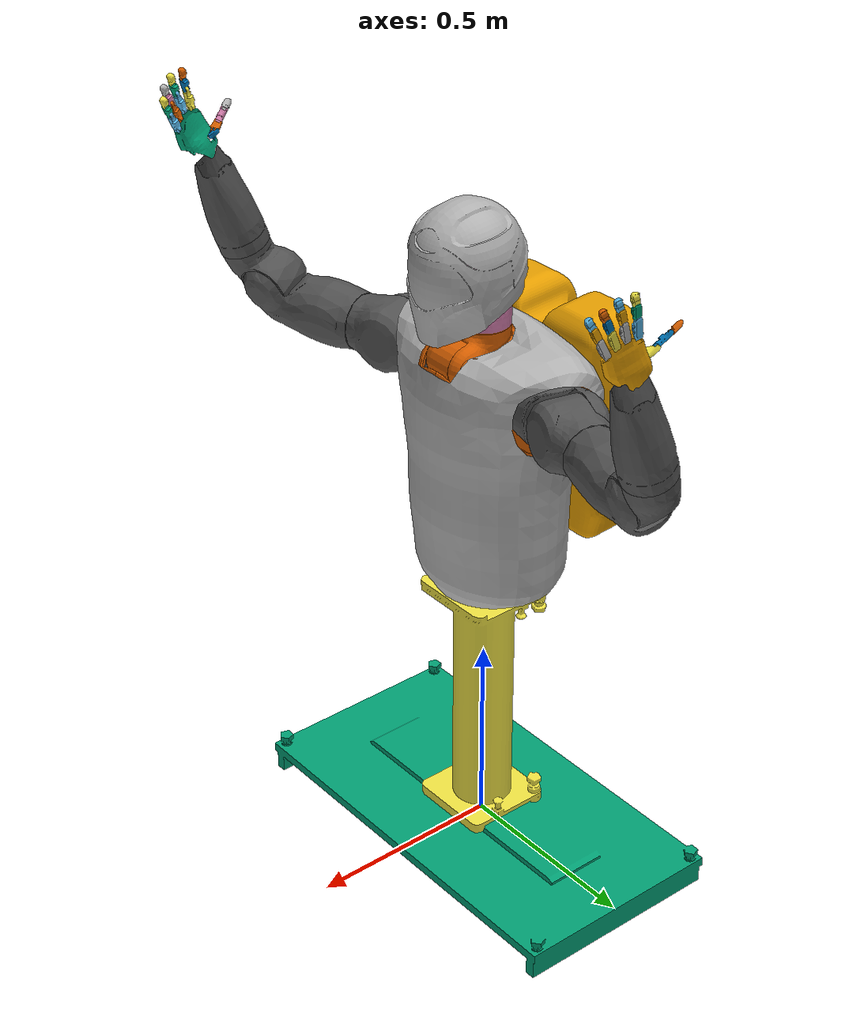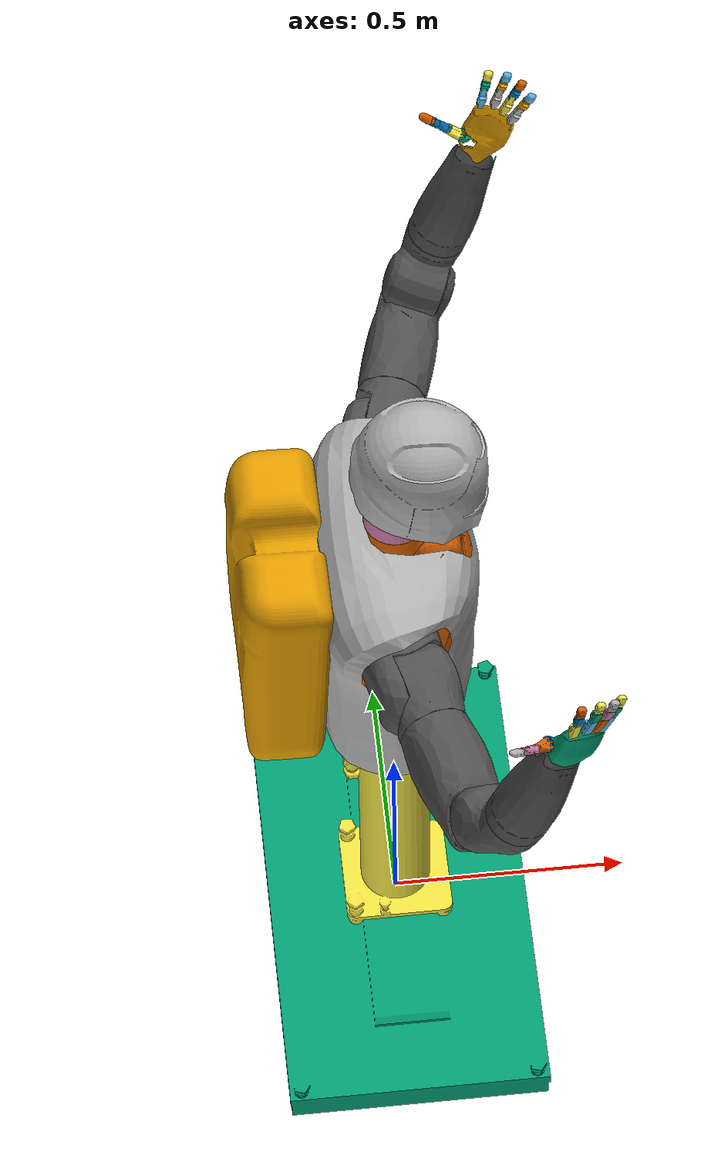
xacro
<?xml version="1.0" ?>

<robot name="r2" xmlns:controller="http://www.ros.org/wiki/controller"
			xmlns:interface="http://www.ros.org/wiki/interface"
			xmlns:sensor="http://www.ros.org/wiki/sensor"
			xmlns:xacro="http://www.ros.org/wiki/xacro">

  <xacro:property name="robot_name" value= "/r2/"/>

  <include filename="$(find r2_description)/robots/r2.urdf.xacro" />

  <include filename="$(find r2_description)/urdf/r2.gazebo.xacro" />
  <include filename="$(find r2_description)/urdf/sensors/r2.gazebo.sensors.xacro" />

</robot>

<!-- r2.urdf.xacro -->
<robot name="r2" xmlns:xacro="http://www.ros.org/wiki/xacro">

  <xacro:property name="robot_name" value= "/r2/"/>

  <include filename="$(find r2_description)/urdf/models/r2.common.xacro" />
  <include filename="$(find r2_description)/urdf/models/r2.base.xacro" />

  <include filename="$(find r2_description)/urdf/models/r2.body.xacro" />
  <include filename="$(find r2_description)/urdf/models/r2.head.xacro" />

  <include filename="$(find r2_description)/urdf/models/r2.left_arm.xacro" />
  <include filename="$(find r2_description)/urdf/models/r2.left_hand.xacro" />

  <include filename="$(find r2_description)/urdf/models/r2.right_arm.xacro" />
  <include filename="$(find r2_description)/urdf/models/r2.right_hand.xacro" />

</robot>

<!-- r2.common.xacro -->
<robot>

  <material name="white">
    <color rgba="1.0 1.0 1.0 1.0"/>
  </material>

  <material name="dirty_white">
    <color rgba="0.322 0.322 0.322 1.0"/>
  </material>

  <material name="gold">
    <color rgba=".878 .49 0.008 1"/>
  </material>

  <material name="steel">
    <color rgba=".7 .7 .7 1"/>
  </material>

  <material name="blue">
    <color rgba="0 0 0.8 1"/>
  </material>

  <macro name="non_visual_link" params="name">
    <link name="${name}">
      <inertial>
        <mass value="0.01"/>
        <inertia ixx="0.0001" ixy="0.0" ixz="0.0" iyy="0.0001" iyz="0.0" izz="0.0001"/>
      </inertial>
    </link>
  </macro>

</robot>

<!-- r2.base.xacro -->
<robot>

  <link name="world"/>

  <joint name="${robot_name}fixed/world/robot_world" type="fixed">
    <parent link="world"/>
    <child link="${robot_name}robot_world"/>
    <origin rpy="0.0 0.0 0.0" xyz="0.0 0.0 0.0"/>
  </joint>

  <link name="${robot_name}robot_world">
    <inertial>
      <mass value="1"/>
      <inertia ixx="1" ixy="0.0" ixz="0.0" iyy="1" iyz="0.0" izz="1"/>
    </inertial>
  </link>

  <joint name="${robot_name}fixed/robot_world/baseplate" type="fixed">
    <parent link="${robot_name}robot_world"/>
    <child link="${robot_name}baseplate"/>
    <origin rpy="0.0 0 3.14159" xyz="0.0 0.0 0.0"/>
  </joint>

  <link name="${robot_name}baseplate">
    <visual>
      <geometry>
        <mesh filename="package://r2_description/meshes/Stanchion_Baseplate.dae"/>
      </geometry>
      <origin xyz="0.0 0.0 0.0" rpy="1.57 0 1.57"/>
    </visual>
    <collision>
      <geometry>
        <mesh filename="package://r2_description/meshes/Stanchion_Baseplate.dae" scale=".01 .01 .01"/>
      </geometry>
      <origin xyz="0.0 0.0 0.0" rpy="1.57 0 1.57"/>
    </collision>
    <inertial>
      <mass value="5"/>
      <inertia ixx="1" ixy="0.0" ixz="0.0" iyy="1" iyz="0.0" izz="1"/>
    </inertial>
  </link>

  <joint name="${robot_name}fixed/baseplate/stanchion" type="fixed">
    <parent link="${robot_name}baseplate"/>
    <child link="${robot_name}stanchion"/>
    <origin rpy="0 0 3.14159" xyz="0.0 0.0 .70"/>
  </joint>

  <link name="${robot_name}stanchion">
    <visual>
      <geometry>
        <mesh filename="package://r2_description/meshes/Stanchion.dae"/>
      </geometry>
      <origin xyz="0.0 0.0 0.0" rpy="0 0 0"/>
    </visual>
    <collision>
      <geometry>
        <cylinder length="0.5" radius=".075"/>
      </geometry>
      <origin xyz="0.0 0.0 -0.3" rpy="0 0 0"/>
    </collision>
    <inertial>
      <mass value="50"/>
      <inertia ixx="10" ixy="0.0" ixz="0.0" iyy="10" iyz="0.0" izz="10"/>
    </inertial>
  </link>

  <joint name="${robot_name}fixed/stanchion/robot_base" type="fixed">
    <parent link="${robot_name}stanchion"/>
    <child link="${robot_name}robot_base"/>
   <origin rpy="0 3.14 3.14" xyz="0.0 0.0 0.02"/>
  </joint>

  <non_visual_link name="${robot_name}robot_base"/>

</robot>

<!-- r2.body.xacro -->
<robot>

  <property name="waist_j0_damping" value= "10.0" />
  <property name="waist_j0_friction" value= "0.0" />

  <joint name="${robot_name}waist/joint0" type="revolute">
    <parent link="${robot_name}robot_base"/>
    <child link="${robot_name}waist_center"/>
    <axis xyz="0 0 1"/>
    <origin rpy="0.0 0 0.0" xyz="0.0 0.0 0.0"/>
    <dynamics damping="${waist_j0_damping}" friction="${waist_j0_friction}"/>
    <limit effort="10000000.0" lower="-3.14" upper="3.14" velocity="1000"/>
  </joint>

  <link name="${robot_name}waist_center">
    <visual>
      <geometry>
         <mesh filename="package://r2_description/meshes/Body.dae"/>
      </geometry>
      <origin rpy="-1.57 0 -1.57" xyz="0.02 0.05 -0.5625"/>
    </visual>
    <collision>
      <geometry>
         <mesh filename="package://r2_description/meshes/Body.dae"/>
      </geometry>
      <origin rpy="-1.57 0 -1.57" xyz="0.02 0.05 -0.5625"/>
    </collision>
    <inertial>
      <mass value="10"/>
      <inertia ixx="1" ixy="0.0" ixz="0.0" iyy="1" iyz="0.0" izz="1"/>
    </inertial>
   </link>

  <joint name="${robot_name}fixed/waist_center/robot_reference" type="fixed">
    <parent link="${robot_name}waist_center"/>
    <child link="${robot_name}robot_reference"/>
    <origin rpy="0.0 0 0.0" xyz="0.1234 0.0 0.0"/>
  </joint>

  <joint name="${robot_name}fixed/waist_center/body_cover" type="fixed">
    <parent link="${robot_name}waist_center"/>
    <child link="${robot_name}body_cover"/>
    <origin rpy="0.0 0.0 0.0" xyz="0 0.0 0.0"/>
  </joint>

  <joint name="${robot_name}fixed/waist_center/backpack" type="fixed">
    <parent link="${robot_name}waist_center"/>
    <child link="${robot_name}backpack"/>
    <origin rpy="0.0 0.0 0.0" xyz="0 0.0 0.0"/>
  </joint>

  <joint name="${robot_name}fixed/waist_center/chest_center" type="fixed">
    <parent link="${robot_name}waist_center"/>
    <child link="${robot_name}chest_center"/>
    <origin rpy="0.0 0.0 0.0" xyz="-0.01235 0.0 0.0"/>
  </joint>

  <joint name="${robot_name}fixed/waist_center/left_shoulder_jr3" type="fixed">
    <parent link="${robot_name}waist_center"/>
    <child link="${robot_name}left_shoulder_jr3"/>
    <origin rpy="0.0 -0.0 0.0 " xyz="-0.0240898 -0.0996837 -0.413899"/>
  </joint>

  <joint name="${robot_name}fixed/waist_center/right_shoulder_jr3" type="fixed">
    <parent link="${robot_name}waist_center"/>
    <child link="${robot_name}right_shoulder_jr3"/>
    <origin rpy="0.0 -0.0 0.0 " xyz="-0.0240898 0.0996837 -0.413899"/>
  </joint>

  <non_visual_link name="${robot_name}robot_reference"/>

  <link name="${robot_name}body_cover">
    <visual>
      <geometry>
         <mesh filename="package://r2_description/meshes/Body_Cover.dae"/>
      </geometry>
      <origin rpy="-1.57 0 -1.57" xyz="0.02 0.05 -0.5625"/>
    </visual>
    <collision>
      <geometry>
         <mesh filename="package://r2_description/meshes/Body_Cover.dae"/>
      </geometry>
      <origin rpy="-1.57 0 -1.57" xyz="0.02 0.05 -0.5625"/>
    </collision>
    <inertial>
        <mass value="0.1"/>
        <inertia ixx="0.001" ixy="0.0" ixz="0.0" iyy="0.001" iyz="0.0" izz="0.001"/>
    </inertial>
  </link>

   <link name="${robot_name}backpack">
    <visual>
      <geometry>
         <mesh filename="package://r2_description/meshes/Backpack.dae"/>
      </geometry>
      <origin rpy="0 0 0.25" xyz="0.0 0.0 -0.54"/>
    </visual>
    <collision>
      <geometry>
         <mesh filename="package://r2_description/meshes/Backpack.dae"/>
      </geometry>
      <origin rpy="0 0 0.25" xyz="0.0 0.0 -0.54"/>
    </collision>
    <inertial>
      <mass value="10"/>
      <inertia ixx="1" ixy="0.0" ixz="0.0" iyy="1" iyz="0.0" izz="1"/>
    </inertial>
  </link>

  <non_visual_link name="${robot_name}chest_center"/>

  <non_visual_link name="${robot_name}left_shoulder_jr3"/>

  <non_visual_link name="${robot_name}right_shoulder_jr3"/>

  <joint name="${robot_name}fixed/chest_center/chest_base" type="fixed">
    <parent link="${robot_name}chest_center"/>
    <child link="${robot_name}chest_base"/>
    <origin rpy="0.0 -0.0 0.0 " xyz="-0.05299202 -0.0 -0.5442458"/>
  </joint>

  <non_visual_link name="${robot_name}chest_base"/>

</robot>

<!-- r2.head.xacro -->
<robot>

  <property name="neck_j0_damping" value= "10.0" />
  <property name="neck_j0_friction" value= "0.0" />
  <property name="neck_j1_damping" value= "10.0" />
  <property name="neck_j1_friction" value= "0.0" />
  <property name="neck_j2_damping" value= "10.0" />
  <property name="neck_j2_friction" value= "0.0" />

  <property name="effort_limit" value= "10000.0" />
  <property name="velocity_limit" value= "1000.0" />

  <joint name="${robot_name}neck/joint0" type="revolute">
    <parent link="${robot_name}waist_center"/>
    <child link="${robot_name}neck_base"/>
    <origin rpy=" -1.570796 -0.0 0.0 " xyz=" 0.08636 0.0 -0.6142228 "/>
    <dynamics damping="${neck_j0_damping}" friction="${neck_j0_friction}"/>
    <axis xyz="0 0 1"/>
    <limit effort="${effort_limit}" lower="-0.7" upper="0.175" velocity="${velocity_limit}"/>
  </joint>

  <link name="${robot_name}neck_base">
    <visual>
      <geometry>
         <mesh filename="package://r2_description/meshes/Neck_Lower.dae"/>
      </geometry>
      <origin rpy="-1.57 1.57 0" xyz="0.0 0.0 0.0"/>
    </visual>
    <inertial>
      <mass value=".1"/>
      <inertia ixx=".0010" ixy="0.0" ixz="0.0" iyy=".0010" iyz="0.0" izz=".0010"/>
    </inertial>
    <collision>
      <geometry>
         <mesh filename="package://r2_description/meshes/Neck_Lower.dae"/>
      </geometry>
      <origin rpy="-1.57 1.57 0" xyz="0.0 0.0 0.0"/>
    </collision>
  </link>

  <joint name="${robot_name}neck/joint1" type="revolute">
    <parent link="${robot_name}neck_base"/>
    <child link="${robot_name}neck_lower_pitch"/>
    <origin rpy=" -1.570796 -0.0 0.0 " xyz=" -0.0762 -0.0 0.0 "/>
    <dynamics damping="${neck_j1_damping}" friction="${neck_j1_friction}"/>
    <axis xyz="0 0 1"/>
    <limit effort="${effort_limit}" lower="-1.22" upper="1.22" velocity="${velocity_limit}"/>
  </joint>

  <link name="${robot_name}neck_lower_pitch">
   <visual>
      <geometry>
         <mesh filename="package://r2_description/meshes/Neck_Upper.dae"/>
      </geometry>
      <origin rpy="0 0 1.57" xyz="0.075 0.0 0.0"/>
    </visual>
    <inertial>
      <mass value=".1"/>
      <inertia ixx=".0010" ixy="0.0" ixz="0.0" iyy=".0010" iyz="0.0" izz=".0010"/>
    </inertial>
    <collision>
      <geometry>
         <mesh filename="package://r2_description/meshes/Neck_Upper.dae"/>
      </geometry>
      <origin rpy="0 0 1.57" xyz="0.075 0.0 0.0"/>
    </collision>
  </link>

  <joint name="${robot_name}neck/joint2" type="revolute">
    <parent link="${robot_name}neck_lower_pitch"/>
    <child link="${robot_name}neck_roll"/>
    <origin rpy=" 1.570796 -0.0 0.0 " xyz=" 0.0508 0.0 0.1777619 "/>
    <dynamics damping="${neck_j2_damping}" friction="${neck_j2_friction}"/>
    <axis xyz="0 0 1"/>
    <limit effort="${effort_limit}" lower="-0.7" upper="0.175" velocity="${velocity_limit}"/>
  </joint>

  <link name="${robot_name}neck_roll">
    <visual>
      <geometry>
         <mesh filename="package://r2_description/meshes/Head.dae"/>
      </geometry>
      <origin rpy="0 1.57 0" xyz="-0.0 0.07 0.0"/>
    </visual>
    <collision>
      <geometry>
         <mesh filename="package://r2_description/meshes/Head.dae"/>
      </geometry>
      <origin rpy="0 1.57 0" xyz="-0.0 0.07 0.0"/>
    </collision>
    <inertial>
      <mass value=".1"/>
      <inertia ixx=".0010" ixy="0.0" ixz="0.0" iyy=".0010" iyz="0.0" izz=".0010"/>
    </inertial>
  </link>

  <joint name="${robot_name}fixed/neck_roll/neck_upper_pitch" type="fixed">
    <parent link="${robot_name}neck_roll"/>
    <child link="${robot_name}neck_upper_pitch"/>
    <origin rpy=" 1.570796 -0.0 0.0 " xyz=" 0.0 0.0 0.0 "/>
  </joint>

  <link name="${robot_name}neck_upper_pitch">
    <inertial>
      <mass value=".1"/>
      <inertia ixx=".0010" ixy="0.0" ixz="0.0" iyy=".0010" iyz="0.0" izz=".0010"/>
    </inertial>
  </link>

  <joint name="${robot_name}fixed/neck_upper_pitch/asus_frame" type="fixed">
    <parent link="${robot_name}neck_upper_pitch"/>
    <child link="${robot_name}asus_frame"/>
     <origin rpy="1.50 0.0 1.57 " xyz="0.12 -0.015 -0.14 "/>
  </joint>

  <joint name="${robot_name}fixed/neck_upper_pitch/simulated_asus_frame" type="fixed">
    <parent link="${robot_name}neck_upper_pitch"/>
    <child link="${robot_name}simulated_asus_frame"/>
    <dynamics damping="1.0" />
    <origin rpy="0 0 0" xyz="0.12 -0.015 -0.14 "/>
  </joint>

  <joint name="${robot_name}fixed/neck_upper_pitch/vision_center_frame" type="fixed">
    <parent link="${robot_name}neck_upper_pitch"/>
    <child link="${robot_name}vision_center_frame"/>
    <dynamics damping="1.0" />
    <origin rpy="1.57 -1.57 1.57" xyz=" 0.066675 0.0 -0.116205 "/>
  </joint>

  <!-- actual asus -->
  <link name="${robot_name}asus_frame">
    <inertial>
      <mass value=".01"/>
      <inertia ixx=".0010" ixy="0.0" ixz="0.0" iyy=".0010" iyz="0.0" izz=".0010"/>
    </inertial>
  </link>

  <joint name="${robot_name}fixed/asus_frame/openni_depth_frame" type="fixed">
    <parent link="${robot_name}asus_frame"/>
    <child link="${robot_name}openni_depth_frame"/>
    <origin rpy="1.57 -1.57 0 " xyz="0 0 0 "/>
  </joint>

 <!-- asus default -->
 <link name="${robot_name}openni_depth_frame">
    <inertial>
      <mass value=".01"/>
      <inertia ixx=".0010" ixy="0.0" ixz="0.0" iyy=".0010" iyz="0.0" izz=".0010"/>
    </inertial>
  </link>

 <!-- simulated asus -->
 <link name="${robot_name}simulated_asus_frame">
    <inertial>
      <mass value=".01"/>
      <inertia ixx=".0010" ixy="0.0" ixz="0.0" iyy=".0010" iyz="0.0" izz=".0010"/>
    </inertial>
  </link>

  <!--visions -->
  <link name="${robot_name}vision_center_frame">
    <inertial>
      <mass value=".1"/>
      <inertia ixx=".0010" ixy="0.0" ixz="0.0" iyy=".0010" iyz="0.0" izz=".0010"/>
    </inertial>
  </link>

  <joint name="${robot_name}fixed/vision_center_frame/left_camera_frame" type="fixed">
    <parent link="${robot_name}vision_center_frame"/>
    <child link="${robot_name}left_camera_frame"/>
    <dynamics damping="1.0" />
    <origin rpy="0 0 1.57" xyz="0.0087 0.04887 0.01789"/>
  </joint>

  <joint name="${robot_name}fixed/vision_center_frame/right_camera_frame" type="fixed">
    <parent link="${robot_name}vision_center_frame"/>
    <child link="${robot_name}right_camera_frame"/>
    <dynamics damping="1.0" />
    <origin rpy="0 0 1.57" xyz="0.0087 -0.04887 0.01789"/>
  </joint>

  <link name="${robot_name}left_camera_frame">
    <inertial>
      <mass value=".1"/>
      <inertia ixx=".0010" ixy="0.0" ixz="0.0" iyy=".0010" iyz="0.0" izz=".0010"/>
    </inertial>
  </link>

  <joint name="${robot_name}fixed/left_camera_frame/left_camera_optical_frame" type="fixed">
    <parent link="${robot_name}left_camera_frame"/>
    <child link="${robot_name}left_camera_optical_frame"/>
    <dynamics damping="1.0" />
    <origin rpy="-1.57 -1.57 0" xyz="0 0 0"/>
  </joint>

  <link name="${robot_name}left_camera_optical_frame">
    <inertial>
      <mass value=".1"/>
      <inertia ixx=".0010" ixy="0.0" ixz="0.0" iyy=".0010" iyz="0.0" izz=".0010"/>
    </inertial>
  </link>

  <link name="${robot_name}right_camera_frame">
    <inertial>
      <mass value=".1"/>
      <inertia ixx=".0010" ixy="0.0" ixz="0.0" iyy=".0010" iyz="0.0" izz=".0010"/>
    </inertial>
  </link>

  <joint name="${robot_name}fixed/right_camera_frame/right_camera_optical_frame" type="fixed">
    <parent link="${robot_name}right_camera_frame"/>
    <child link="${robot_name}right_camera_optical_frame"/>
    <dynamics damping="1.0" />
    <origin rpy="-1.57 -1.57 0" xyz="0 0 0"/>
  </joint>

  <link name="${robot_name}right_camera_optical_frame">
    <inertial>
      <mass value=".1"/>
      <inertia ixx=".0010" ixy="0.0" ixz="0.0" iyy=".0010" iyz="0.0" izz=".0010"/>
    </inertial>
  </link>

</robot>

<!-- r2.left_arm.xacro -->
<robot>

  <property name="left_arm_j0_damping" value= "10.0" />
  <property name="left_arm_j0_friction" value= "0.0" />
  <property name="left_arm_j1_damping" value= "10.0" />
  <property name="left_arm_j1_friction" value= "0.0" />
  <property name="left_arm_j2_damping" value= "10.0" />
  <property name="left_arm_j2_friction" value= "0.0" />
  <property name="left_arm_j3_damping" value= "1.0" />
  <property name="left_arm_j3_friction" value= "0.0" />
  <property name="left_arm_j4_damping" value= "1.0" />
  <property name="left_arm_j4_friction" value= "0.0" />
  <property name="left_arm_j5_damping" value= "1.0" />
  <property name="left_arm_j5_friction" value= "0.0" />
  <property name="left_arm_j6_damping" value= "1.0" />
  <property name="left_arm_j6_friction" value= "0.0" />

  <joint name="${robot_name}left_arm/joint0" type="revolute">
    <parent link="${robot_name}chest_base"/>
    <child link="${robot_name}left_shoulder_roll"/>
    <origin rpy=" -1.5664 -0.0 -2.8802 " xyz=" -0.0 -0.0 0.0 "/>
    <axis xyz="0 0 1"/>
    <dynamics damping="${left_arm_j0_damping}" friction="${left_arm_j0_friction}"/>
    <limit effort="100.0" lower="-1.57" upper="1.57" velocity="1000"/>
  </joint>

  <link name="${robot_name}left_shoulder_roll">
    <visual>
      <geometry>
        <mesh filename="package://r2_description/meshes/Left_Shoulder_Upper.dae"/>
      </geometry>
      <material name="dirty_white"/>
      <origin rpy="0 0 1.57" xyz="0 0 .08"/>
    </visual>
    <collision>
      <geometry>
        <mesh filename="package://r2_description/meshes/Left_Shoulder_Upper.dae"/>
      </geometry>
      <origin rpy="0 0 1.57" xyz="0 0 .08"/>
    </collision>
    <inertial>
	<origin xyz="-0.0089916 -0.00131572   0.10287   "/>
        <mass value="6.168856232"/>
        <inertia ixx="0.0198585269"  ixy="-0.0060195977"  ixz="-0.0003950635"  iyy="0.0671900643"  iyz="0.00012683"  izz="0.0634150128"/>
    </inertial>
  </link>

  <joint name="${robot_name}left_arm/joint1" type="revolute">
    <parent link="${robot_name}left_shoulder_roll"/>
    <child link="${robot_name}left_shoulder_pitch"/>
    <origin rpy=" -1.5701 -0.0 1.570796 " xyz=" 0.0 0.0 0.316611 "/>
    <axis xyz="0 0 1"/>
    <dynamics damping="${left_arm_j1_damping}" friction="${left_arm_j1_friction}"/>
    <limit effort="100.0" lower="-1.66" upper=".175" velocity="1000"/>
  </joint>

  <link name="${robot_name}left_shoulder_pitch">
    <visual>
      <geometry>
        <mesh filename="package://r2_description/meshes/Left_Shoulder_Lower.dae"/>
      </geometry>
      <material name="dirty_white"/>
      <origin rpy=".0 0 -1.57" xyz="0 0 0"/>
    </visual>
    <collision>
      <geometry>
        <mesh filename="package://r2_description/meshes/Left_Shoulder_Lower.dae"/>
      </geometry>
      <origin rpy=".0 0 -1.57" xyz="0 0 0"/>
    </collision>
     <inertial>
        <origin xyz="0.037084 -0.00028448   0.0077978   "/>
        <mass value="4.4270615312"/>
        <inertia ixx="0.02701064"  ixy="0.001512947"  ixz="-0.000052382497887"  iyy="0.0113836825"  iyz="0.0000217138622526"  izz="0.0251962741"/>
    </inertial>
  </link>

  <joint name="${robot_name}left_arm/joint2" type="revolute">
    <parent link="${robot_name}left_shoulder_pitch"/>
    <child link="${robot_name}left_upper_arm"/>
    <origin rpy=" 1.57 -0.0 0.0 " xyz=" 0.0 0.0 0.0 "/>
    <axis xyz="0 0 1"/>
    <dynamics damping="${left_arm_j2_damping}" friction="${left_arm_j2_friction}"/>
    <limit effort="100.0" lower="-4.89" upper="-0.79" velocity="1000"/>
  </joint>

  <link name="${robot_name}left_upper_arm">
    <visual>
      <geometry>
        <mesh filename="package://r2_description/meshes/Left_Upper_Arm.dae"/>
      </geometry>
      <material name="dirty_white"/>
      <origin rpy="0 0 3.14" xyz="0 0 .1016"/>
    </visual>
    <collision>
      <geometry>
        <mesh filename="package://r2_description/meshes/Left_Upper_Arm.dae"/>
      </geometry>
      <origin rpy="0 0 3.14" xyz="0 0 .1016"/>
    </collision>
    <inertial>
        <origin xyz="-0.0074168 -0.041402   0.1016   "/>
        <mass value="4.853438359"/>
        <inertia ixx="0.016007389"  ixy="-0.00339462"  ixz="0.0065843922"  iyy="0.0462370652"  iyz="0.0013754064"  izz="0.04214011"/>
    </inertial>
  </link>

  <joint name="${robot_name}left_arm/joint3" type="revolute">
    <parent link="${robot_name}left_upper_arm"/>
    <child link="${robot_name}left_elbow"/>
    <origin rpy=" -1.5748 -0.0 0.0 " xyz=" -0.05437886 -0.0 0.3564382 "/>
    <axis xyz="0 0 1"/>
    <dynamics damping="${left_arm_j3_damping}" friction="${left_arm_j3_friction}"/>
    <limit effort="100.0" lower="-2.79" upper="-.087" velocity="1000"/>
  </joint>

  <link name="${robot_name}left_elbow">
    <visual>
      <geometry>
        <mesh filename="package://r2_description/meshes/Left_Elbow.dae"/>
      </geometry>
      <material name="dirty_white"/>
      <origin rpy="0 0 -1.57" xyz="0 0 0"/>
    </visual>
    <collision>
      <geometry>
        <mesh filename="package://r2_description/meshes/Left_Elbow.dae"/>
      </geometry>
      <origin rpy="0 0 -1.57" xyz="0 0 0"/>
    </collision>
    <inertial>
        <origin xyz="0.026162 0.033782   0.0154432   "/>
        <mass value="2.9710300235"/>
        <inertia ixx="0.0120274897"  ixy="0.0016417085"  ixz="-0.001188117"  iyy="0.0088377175"  iyz="0.0031605083"  izz="0.0105350275"/>
    </inertial>
  </link>

  <joint name="${robot_name}left_arm/joint4" type="revolute">
    <parent link="${robot_name}left_elbow"/>
    <child link="${robot_name}left_lower_arm"/>
    <origin rpy=" 1.5738 -0.0 0.0 " xyz=" 0.0540385 0.0 0.0 "/>
    <axis xyz="0 0 1"/>
    <dynamics damping="${left_arm_j4_damping}" friction="${left_arm_j4_friction}"/>
    <limit effort="100.0" lower="-1.3" upper="4.45" velocity="1000"/>
  </joint>

  <link name="${robot_name}left_lower_arm">
    <visual>
      <geometry>
        <mesh filename="package://r2_description/meshes/Left_Forearm.dae"/>
      </geometry>
      <origin xyz="0 0 0.1"/>
      <material name="dirty_white"/>
    </visual>
    <collision>
      <geometry>
        <mesh filename="package://r2_description/meshes/Left_Forearm.dae"/>
      </geometry>
      <origin xyz="0 0 0.1"/>
    </collision>
    <inertial>
        <origin xyz="0.0003556 -0.00122682   0.17653   "/>
        <mass value="6.939963261"/>
        <inertia ixx="0.0125249771"  ixy="-0.0002446467"  ixz="0.0005208986"  iyy="0.0395063532"  iyz="-0.0001691457"  izz="0.0403842721"/>
    </inertial>
  </link>

  <joint name="${robot_name}left_arm/joint5" type="revolute">
    <parent link="${robot_name}left_lower_arm"/>
    <child link="${robot_name}left_wrist_pitch"/>
    <origin rpy=" -1.5952 -0.0 0.0 " xyz=" 0.0 0.0 0.3570478 "/>
    <axis xyz="0 0 1"/>
    <dynamics damping="${left_arm_j5_damping}" friction="${left_arm_j5_friction}"/>
    <limit effort="100.0" lower="-1.22" upper="1.22" velocity="1000"/>
  </joint>

  <link name="${robot_name}left_wrist_pitch">
    <inertial>
        <origin xyz="-0.004064   0.000000152908   -0.00092202"/>
        <mass value="0.1165732391"/>
        <inertia ixx="0.00005765"  ixy="0.00000000004360"  ixz="0.00000175876"  iyy="0.0000169438359087"  iyz="0.000000054430975458"  izz="0.000044188587603"/>
    </inertial>
  </link>

  <joint name="${robot_name}left_arm/joint6" type="revolute">
    <parent link="${robot_name}left_wrist_pitch"/>
    <child link="${robot_name}left_wrist_yaw"/>
    <origin rpy=" 1.6505 -0.0 -1.5727 " xyz=" -0.00001156 -0.006072621 0.0 "/>
    <axis xyz="0 0 1"/>
    <dynamics damping="${left_arm_j6_damping}" friction="${left_arm_j6_friction}"/>
    <limit effort="100.0" lower="-0.785" upper="0.785" velocity="1000"/>
  </joint>

  <link name="${robot_name}left_wrist_yaw">
    <inertial>
        <origin xyz="-0.00090932   -0.0253746  0.067564     "/>
        <mass value="1.1884120094"/>
        <inertia ixx="0.0044481227"  ixy="0.0003716524"  ixz="0.0001024239"  iyy="0.0030141884"  iyz="0.000101546"  izz="0.001992876"/>
    </inertial>
  </link>

  <joint name="${robot_name}fixed/left_wrist_yaw/left_palm" type="fixed">
    <parent link="${robot_name}left_wrist_yaw"/>
    <child link="${robot_name}left_palm"/>
    <origin rpy=" 0.0 -0.0 -0.014 " xyz=" 0.0 -0.0 0.0 "/>
  </joint>

  <link name="${robot_name}left_palm">
    <visual>
      <geometry>
        <mesh filename="package://r2_description/meshes/Left_Palm.dae"/>
      </geometry>
      <origin xyz="0.0 0.0 -0.0" rpy="3.14 0 1.57"/>
    </visual>
    <collision>
      <geometry>
        <mesh filename="package://r2_description/meshes/Left_Palm.dae"/>
      </geometry>
      <origin xyz="0.0 0.0 -0.0" rpy="3.14 0 1.57"/>
    </collision>
    <inertial>
        <origin xyz="0.067564   -0.0253746   -0.00090932"/>
        <mass value="1.1884120094"/>
        <inertia ixx="0.001992876"  ixy="0.000101546"  ixz="0.0001024239"  iyy="0.0030141884"  iyz="0.0003716524"  izz="0.0044481227"/>
    </inertial>
  </link>

</robot>

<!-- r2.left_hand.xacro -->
<robot>

  <property name="left_arm_hand_thumb_j0_damping" value= "0.1" />
  <property name="left_arm_hand_thumb_j0_friction" value= "0.0" />
  <property name="left_arm_hand_thumb_j1_damping" value= "0.1" />
  <property name="left_arm_hand_thumb_j1_friction" value= "0.0" />
  <property name="left_arm_hand_thumb_j2_damping" value= "0.1" />
  <property name="left_arm_hand_thumb_j2_friction" value= "0.0" />
  <property name="left_arm_hand_thumb_j3_damping" value= "0.1" />
  <property name="left_arm_hand_thumb_j3_friction" value= "0.0" />

  <property name="left_arm_hand_index_j0_damping" value= "0.1" />
  <property name="left_arm_hand_index_j0_friction" value= "0.0" />
  <property name="left_arm_hand_index_j1_damping" value= "0.1" />
  <property name="left_arm_hand_index_j1_friction" value= "0.0" />
  <property name="left_arm_hand_index_j2_damping" value= "0.1" />
  <property name="left_arm_hand_index_j2_friction" value= "0.0" />
  <property name="left_arm_hand_index_j3_damping" value= "0.1" />
  <property name="left_arm_hand_index_j3_friction" value= "0.0" />

  <property name="left_arm_hand_middle_j0_damping" value= "0.1" />
  <property name="left_arm_hand_middle_j0_friction" value= "0.0" />
  <property name="left_arm_hand_middle_j1_damping" value= "0.1" />
  <property name="left_arm_hand_middle_j1_friction" value= "0.0" />
  <property name="left_arm_hand_middle_j2_damping" value= "0.1" />
  <property name="left_arm_hand_middle_j2_friction" value= "0.0" />
  <property name="left_arm_hand_middle_j3_damping" value= "0.1" />
  <property name="left_arm_hand_middle_j3_friction" value= "0.0" />

  <property name="left_arm_hand_ring_j0_damping" value= "0.1" />
  <property name="left_arm_hand_ring_j0_friction" value= "0.0" />
  <property name="left_arm_hand_ring_j1_damping" value= "0.1" />
  <property name="left_arm_hand_ring_j1_friction" value= "0.0" />
  <property name="left_arm_hand_ring_j2_damping" value= "0.1" />
  <property name="left_arm_hand_ring_j2_friction" value= "0.0" />

  <property name="left_arm_hand_little_j0_damping" value= "0.1" />
  <property name="left_arm_hand_little_j0_friction" value= "0.0" />
  <property name="left_arm_hand_little_j1_damping" value= "0.1" />
  <property name="left_arm_hand_little_j1_friction" value= "0.0" />
  <property name="left_arm_hand_little_j2_damping" value= "0.1" />
  <property name="left_arm_hand_little_j2_friction" value= "0.0" />

  <joint name="${robot_name}left_arm/hand/thumb/joint0" type="revolute">
    <parent link="${robot_name}left_wrist_yaw"/>
    <child link="${robot_name}left_thumb_base"/>
    <origin xyz=" 0.03302 0.03048 0.00635 " rpy=" -1.57079632679 -0.0 1.30899702752 " />
    <axis xyz="0 0 1"/>
    <limit effort="10000000.0" lower="-1.2217" upper="0.0" velocity="1000"/>
    <dynamics damping="${left_arm_hand_thumb_j0_damping}" friction="${left_arm_hand_thumb_j0_friction}"/>
  </joint>

  <joint name="${robot_name}fixed/left_index_base/left_index_base" type="fixed">
    <parent link="${robot_name}left_wrist_yaw"/>
    <child link="${robot_name}left_index_base"/>
    <origin xyz=" 0.0994646728 0.0271119346 -0.0161544 " rpy=" 0.0 -0.0 0.122172725275 " />
  </joint>

  <joint name="${robot_name}left_arm/hand/index/joint0" type="revolute">
    <parent link="${robot_name}left_index_base"/>
    <child link="${robot_name}left_index_yaw"/>
    <origin xyz="0.0 0.0 0.0" rpy="0.0 0.0 0.0" />
    <axis xyz="0 0 1"/>
    <limit effort="10000000.0" lower="-0.3491" upper="0.3491" velocity="1000"/>
    <dynamics damping="${left_arm_hand_index_j0_damping}" friction="${left_arm_hand_index_j0_friction}"/>
  </joint>

  <joint name="${robot_name}fixed/left_middle_base/left_middle_base" type="fixed">
    <parent link="${robot_name}left_wrist_yaw"/>
    <child link="${robot_name}left_middle_base"/>
    <origin xyz=" 0.10646537 0.00254 -0.0161544 " rpy=" 0.0 -0.0 0.0 " />
  </joint>

  <joint name="${robot_name}left_arm/hand/middle/joint0" type="revolute">
    <parent link="${robot_name}left_middle_base"/>
    <child link="${robot_name}left_middle_yaw"/>
    <origin xyz="0.0 0.0 0.0" rpy="0.0 0.0 0.0" />
    <axis xyz="0 0 1"/>
    <limit effort="10000000.0" lower="-0.3491" upper="0.3491" velocity="1000"/>
    <dynamics damping="${left_arm_hand_middle_j0_damping}" friction="${left_arm_hand_middle_j0_friction}"/>
  </joint>

  <joint name="${robot_name}left_arm/hand/ring/joint0" type="revolute">
    <parent link="${robot_name}left_wrist_yaw"/>
    <child link="${robot_name}left_ring_proximal"/>
    <origin xyz=" 0.1084570602 -0.0197673468 -0.012319 " rpy=" 1.57079632679 -0.0 -0.122172725275 " />
    <axis xyz="0 0 1"/>
    <limit effort="10000000.0" lower="0" upper="2.9671" velocity="1000"/>
    <dynamics damping="${left_arm_hand_ring_j0_damping}" friction="${left_arm_hand_ring_j0_friction}"/>
  </joint>

  <joint name="${robot_name}left_arm/hand/little/joint0" type="revolute">
    <parent link="${robot_name}left_wrist_yaw"/>
    <child link="${robot_name}left_little_proximal"/>
    <origin xyz=" 0.094635701 -0.0403792436 -0.0060878212 " rpy=" 1.60570321374 -0.0872667473393 -0.17453258148 " />
    <axis xyz="0 0 1"/>
    <limit effort="10000000.0" lower="0" upper="2.9671" velocity="1000"/>
    <dynamics damping="${left_arm_hand_little_j0_damping}" friction="${left_arm_hand_little_j0_friction}"/>
  </joint>

  <link name="${robot_name}left_thumb_base">
    <inertial>
      <mass value=".05"/>
      <inertia ixx=".0010" ixy="0.0" ixz="0.0" iyy=".0010" iyz="0.0" izz=".0010"/>
    </inertial>
  </link>

  <joint name="${robot_name}fixed/left_thumb_base/left_thumb_proximal" type="fixed">
    <parent link="${robot_name}left_thumb_base"/>
    <child link="${robot_name}left_thumb_proximal"/>
    <origin xyz=" 0.011938 0.0 0.0 " rpy=" -1.570796 -0.0 0.0 " />
  </joint>

  <link name="${robot_name}left_thumb_proximal">
    <inertial>
      <mass value=".0010"/>
      <inertia ixx=".0010" ixy="0.0" ixz="0.0" iyy=".0010" iyz="0.0" izz=".0010"/>
    </inertial>
    <visual>
      <geometry>
        <mesh filename="package://r2_description/meshes/Left_Thumb_Carp.dae"/>
      </geometry>
      <origin xyz="-0.01 0.0 0.0" rpy="-1.57 0 0"/>
    </visual>
    <collision>
      <geometry>
        <mesh filename="package://r2_description/meshes/Left_Thumb_Carp.dae"/>
      </geometry>
      <origin xyz="-0.01 0.0 0.0" rpy="-1.57 0 0"/>
    </collision>
  </link>

  <joint name="${robot_name}left_arm/hand/thumb/joint1" type="revolute">
    <parent link="${robot_name}left_thumb_proximal"/>
    <child link="${robot_name}left_thumb_medial_prime"/>
    <origin xyz=" 0.0 0.0 0.0 " rpy=" 0.0 -0.0 0.0 " />
    <axis xyz="0 0 1"/>
    <limit effort="10000000.0" lower="0.0" upper="1.3963" velocity="1000"/>
    <dynamics damping="${left_arm_hand_thumb_j1_damping}" friction="${left_arm_hand_thumb_j1_friction}"/>
  </joint>

  <link name="${robot_name}left_thumb_medial_prime">
    <inertial>
      <mass value=".0010"/>
      <inertia ixx=".0010" ixy="0.0" ixz="0.0" iyy=".0010" iyz="0.0" izz=".0010"/>
    </inertial>
     <visual>
       <geometry>
        <mesh filename="package://r2_description/meshes/Left_Thumb_MtCar.dae"/>
      </geometry>
      <origin xyz="-0.0 0 0.0" rpy="-1.57 -1.57 0"/>
    </visual>
    <collision>
      <geometry>
        <mesh filename="package://r2_description/meshes/Left_Thumb_MtCar.dae"/>
      </geometry>
      <origin xyz="0.0 0.0 0.0" rpy="-1.57 -1.57 0"/>
    </collision>
  </link>

  <joint name="${robot_name}left_arm/hand/thumb/joint2" type="revolute">
    <parent link="${robot_name}left_thumb_medial_prime"/>
    <child link="${robot_name}left_thumb_medial"/>
    <origin xyz=" 0.030734 -0.001905 0.00254 " rpy=" -0.698132284627 -0.0 0.0 " />
    <axis xyz="0 0 1"/>
    <limit effort="10000000.0" lower="0.0" upper="1.2217" velocity="1000"/>
    <dynamics damping="${left_arm_hand_thumb_j2_damping}" friction="${left_arm_hand_thumb_j2_friction}"/>
  </joint>

  <link name="${robot_name}left_thumb_medial">
    <inertial>
      <mass value=".0010"/>
      <inertia ixx=".0010" ixy="0.0" ixz="0.0" iyy=".0010" iyz="0.0" izz=".0010"/>
    </inertial>
    <visual>
       <geometry>
        <mesh filename="package://r2_description/meshes/Thumb_Proximal.dae"/>
      </geometry>
      <origin xyz="0.0 0.0 0.0" rpy="3.14 0 1.57"/>
    </visual>
    <collision>
      <geometry>
        <mesh filename="package://r2_description/meshes/Thumb_Proximal.dae"/>
      </geometry>
      <origin xyz="0.0 0.0 0.0" rpy="3.14 0 1.57"/>
    </collision>
  </link>

  <joint name="${robot_name}left_arm/hand/thumb/joint3" type="revolute">
    <parent link="${robot_name}left_thumb_medial"/>
    <child link="${robot_name}left_thumb_distal"/>
    <origin xyz=" 0.03937 0.0 0.0 " rpy=" 0.0 -0.0 0.0 " />
    <axis xyz="0 0 1"/>
    <limit effort="10000000.0" lower="-0.5236" upper="1.57" velocity="1000"/>
    <dynamics damping="${left_arm_hand_thumb_j3_damping}" friction="${left_arm_hand_thumb_j3_friction}"/>
  </joint>

  <link name="${robot_name}left_thumb_distal">
    <inertial>
      <mass value=".0010"/>
      <inertia ixx=".0010" ixy="0.0" ixz="0.0" iyy=".0010" iyz="0.0" izz=".0010"/>
    </inertial>
    <visual>
       <geometry>
        <mesh filename="package://r2_description/meshes/Thumb_Dist.dae"/>
      </geometry>
      <origin xyz="0.0 0.0 0.0" rpy="3.14 3.14 0"/>
    </visual>
    <collision>
      <geometry>
        <mesh filename="package://r2_description/meshes/Thumb_Dist.dae"/>
      </geometry>
      <origin xyz="0.0 0.0 0.0" rpy="3.14 3.14 0"/>
    </collision>
  </link>

  <joint name="${robot_name}fixed/left_thumb_distal/left_thumb_tip" type="fixed">
    <parent link="${robot_name}left_thumb_distal"/>
    <child link="${robot_name}left_thumb_tip"/>
    <origin xyz=" 0.03302 0.0 0.0 " rpy=" 0.0 -0.0 0.0 " />
  </joint>

  <link name="${robot_name}left_thumb_tip">
    <inertial>
      <mass value=".0010"/>
      <inertia ixx=".0010" ixy="0.0" ixz="0.0" iyy=".0010" iyz="0.0" izz=".0010"/>
    </inertial>
  </link>

  <link name="${robot_name}left_index_base">
    <inertial>
      <mass value=".0010"/>
      <inertia ixx=".0010" ixy="0.0" ixz="0.0" iyy=".0010" iyz="0.0" izz=".0010"/>
    </inertial>
  </link>

  <link name="${robot_name}left_index_yaw">
    <inertial>
      <mass value=".0010"/>
      <inertia ixx=".0010" ixy="0.0" ixz="0.0" iyy=".0010" iyz="0.0" izz=".0010"/>
    </inertial>
  </link>

  <joint name="${robot_name}left_arm/hand/index/joint1" type="revolute">
    <parent link="${robot_name}left_index_yaw"/>
    <child link="${robot_name}left_index_proximal"/>
    <origin xyz=" 0.009652 0.0 0.0 " rpy=" 1.570796 0.0 0.0 " />
    <axis xyz="0 0 1"/>
    <limit effort="10000000.0" lower="0.0" upper="1.57" velocity="1000"/>
    <dynamics damping="${left_arm_hand_index_j1_damping}" friction="${left_arm_hand_index_j1_friction}"/>
  </joint>

  <link name="${robot_name}left_index_proximal">
    <inertial>
      <mass value=".0010"/>
      <inertia ixx=".0010" ixy="0.0" ixz="0.0" iyy=".0010" iyz="0.0" izz=".0010"/>
    </inertial>
    <visual>
      <geometry>
        <mesh filename="package://r2_description/meshes/Finger_Proximal.dae"/>
      </geometry>
      <origin xyz="0.0 0.0 0.0" rpy="0 0 1.57"/>
    </visual>
    <collision>
      <geometry>
        <mesh filename="package://r2_description/meshes/Finger_Proximal.dae"/>
      </geometry>
      <origin xyz="0.0 0.0 0.0" rpy="0 0 1.57"/>
    </collision>
  </link>

  <joint name="${robot_name}left_arm/hand/index/joint2" type="revolute">
    <parent link="${robot_name}left_index_proximal"/>
    <child link="${robot_name}left_index_medial"/>
    <origin xyz=" 0.04445 0.0 0.0 " rpy=" 0.0 -0.0 0.0 " />
    <axis xyz="0 0 1"/>
    <limit effort="10000000.0" lower="0.0" upper="1.57" velocity="1000"/>
    <dynamics damping="${left_arm_hand_index_j2_damping}" friction="${left_arm_hand_index_j2_friction}"/>
  </joint>

  <link name="${robot_name}left_index_medial">
    <inertial>
      <mass value=".0010"/>
      <inertia ixx=".0010" ixy="0.0" ixz="0.0" iyy=".0010" iyz="0.0" izz=".0010"/>
    </inertial>
    <visual>
      <geometry>
        <mesh filename="package://r2_description/meshes/Finger_Mid.dae"/>
      </geometry>
      <origin xyz="0.0 0.0 0.0" rpy="3.14 0 1.57"/>
    </visual>
    <collision>
      <geometry>
        <mesh filename="package://r2_description/meshes/Finger_Mid.dae"/>
      </geometry>
      <origin xyz="0.0 0.0 0.0" rpy="3.14 0 1.57"/>
    </collision>
  </link>

  <joint name="${robot_name}left_arm/hand/index/joint3" type="revolute">
    <parent link="${robot_name}left_index_medial"/>
    <child link="${robot_name}left_index_distal"/>
    <origin xyz=" 0.03048 0.0 0.0 " rpy=" 0.0 -0.0 0.0 " />
    <axis xyz="0 0 1"/>
    <limit effort="10000000.0" lower="0.0" upper="1.57" velocity="1000"/>
    <dynamics damping="${left_arm_hand_index_j3_damping}" friction="${left_arm_hand_index_j3_friction}"/>
  </joint>

  <link name="${robot_name}left_index_distal">
    <inertial>
      <mass value=".0010"/>
      <inertia ixx=".0010" ixy="0.0" ixz="0.0" iyy=".0010" iyz="0.0" izz=".0010"/>
    </inertial>
    <visual>
      <geometry>
        <mesh filename="package://r2_description/meshes/Finger_Dist.dae"/>
      </geometry>
      <origin xyz="0.0 0.0 0.0" rpy="0 -1.57 0"/>
    </visual>
    <collision>
      <geometry>
        <mesh filename="package://r2_description/meshes/Finger_Dist.dae"/>
      </geometry>
      <origin xyz="0.0 0.0 0.0" rpy="0 -1.57 0"/>
    </collision>
  </link>

  <joint name="${robot_name}fixed/left_index_distal/left_index_tip" type="fixed">
    <parent link="${robot_name}left_index_distal"/>
    <child link="${robot_name}left_index_tip"/>
    <origin xyz=" 0.024638 0.0 0.0 " rpy=" 0.0 -0.0 0.0 " />
  </joint>

  <link name="${robot_name}left_index_tip">
    <inertial>
      <mass value=".0010"/>
      <inertia ixx=".0010" ixy="0.0" ixz="0.0" iyy=".0010" iyz="0.0" izz=".0010"/>
    </inertial>
  </link>

  <link name="${robot_name}left_middle_base">
    <inertial>
      <mass value=".0010"/>
      <inertia ixx=".0010" ixy="0.0" ixz="0.0" iyy=".0010" iyz="0.0" izz=".0010"/>
    </inertial>
  </link>

  <link name="${robot_name}left_middle_yaw">
    <inertial>
      <mass value=".0010"/>
      <inertia ixx=".0010" ixy="0.0" ixz="0.0" iyy=".0010" iyz="0.0" izz=".0010"/>
    </inertial>
  </link>

  <joint name="${robot_name}left_arm/hand/middle/joint1" type="revolute">
    <parent link="${robot_name}left_middle_yaw"/>
    <child link="${robot_name}left_middle_proximal"/>
    <origin xyz=" 0.009652 0.0 0.0 " rpy=" 1.570796 -0.0 0.0 " />
    <axis xyz="0 0 1"/>
    <limit effort="10000000.0" lower="0.0" upper="1.57" velocity="1000"/>
    <dynamics damping="${left_arm_hand_middle_j1_damping}" friction="${left_arm_hand_middle_j1_friction}"/>
  </joint>

  <link name="${robot_name}left_middle_proximal">
    <inertial>
      <mass value=".0010"/>
      <inertia ixx=".0010" ixy="0.0" ixz="0.0" iyy=".0010" iyz="0.0" izz=".0010"/>
    </inertial>
    <visual>
      <geometry>
        <mesh filename="package://r2_description/meshes/Finger_Proximal.dae"/>
      </geometry>
      <origin xyz="0.0 0.0 0.0" rpy="0 0 1.57"/>
    </visual>
    <collision>
      <geometry>
        <mesh filename="package://r2_description/meshes/Finger_Proximal.dae"/>
      </geometry>
      <origin xyz="0.0 0.0 0.0" rpy="0 0 1.57"/>
    </collision>
  </link>

  <joint name="${robot_name}left_arm/hand/middle/joint2" type="revolute">
    <parent link="${robot_name}left_middle_proximal"/>
    <child link="${robot_name}left_middle_medial"/>
    <origin xyz=" 0.04445 0.0 0.0 " rpy=" 0.0 -0.0 0.0 " />
    <axis xyz="0 0 1"/>
    <limit effort="10000000.0" lower="0.0" upper="1.57" velocity="1000"/>
    <dynamics damping="${left_arm_hand_middle_j2_damping}" friction="${left_arm_hand_middle_j2_friction}"/>
  </joint>

  <link name="${robot_name}left_middle_medial">
    <inertial>
      <mass value=".0010"/>
      <inertia ixx=".0010" ixy="0.0" ixz="0.0" iyy=".0010" iyz="0.0" izz=".0010"/>
    </inertial>
    <visual>
      <geometry>
        <mesh filename="package://r2_description/meshes/Finger_Mid.dae"/>
      </geometry>
      <origin xyz="0.0 0.0 0.0" rpy="3.14 0 1.57"/>
    </visual>
    <collision>
      <geometry>
        <mesh filename="package://r2_description/meshes/Finger_Mid.dae"/>
      </geometry>
      <origin xyz="0.0 0.0 0.0" rpy="3.14 0 1.57"/>
    </collision>
  </link>

  <joint name="${robot_name}left_arm/hand/middle/joint3" type="revolute">
    <parent link="${robot_name}left_middle_medial"/>
    <child link="${robot_name}left_middle_distal"/>
    <origin xyz=" 0.03048 0.0 0.0 " rpy=" 0.0 -0.0 0.0 " />
    <axis xyz="0 0 1"/>
    <limit effort="10000000.0" lower="0.0" upper="1.57" velocity="1000"/>
    <dynamics damping="${left_arm_hand_middle_j3_damping}" friction="${left_arm_hand_middle_j3_friction}"/>
  </joint>

  <link name="${robot_name}left_middle_distal">
    <inertial>
      <mass value=".0010"/>
      <inertia ixx=".0010" ixy="0.0" ixz="0.0" iyy=".0010" iyz="0.0" izz=".0010"/>
    </inertial>
    <visual>
      <geometry>
        <mesh filename="package://r2_description/meshes/Finger_Dist.dae"/>
      </geometry>
      <origin xyz="0.0 0.0 0.0" rpy="0 -1.57 0"/>
    </visual>
    <collision>
      <geometry>
        <mesh filename="package://r2_description/meshes/Finger_Dist.dae"/>
      </geometry>
      <origin xyz="0.0 0.0 0.0" rpy="0 -1.57 0"/>
    </collision>
  </link>

  <joint name="${robot_name}fixed/left_middle_distal/left_middle_tip" type="fixed">
    <parent link="${robot_name}left_middle_distal"/>
    <child link="${robot_name}left_middle_tip"/>
    <origin xyz=" 0.024638 0.0 0.0 " rpy=" 0.0 -0.0 0.0 " />
  </joint>

  <link name="${robot_name}left_middle_tip">
    <inertial>
      <mass value=".0010"/>
      <inertia ixx=".0010" ixy="0.0" ixz="0.0" iyy=".0010" iyz="0.0" izz=".0010"/>
    </inertial>
  </link>

  <link name="${robot_name}left_ring_proximal">
    <inertial>
      <mass value=".0010"/>
      <inertia ixx=".0010" ixy="0.0" ixz="0.0" iyy=".0010" iyz="0.0" izz=".0010"/>
    </inertial>
    <visual>
      <geometry>
        <mesh filename="package://r2_description/meshes/Finger_Proximal.dae"/>
      </geometry>
      <origin xyz="0.0 0.0 0.0" rpy="0 0 1.57"/>
    </visual>
    <collision>
      <geometry>
        <mesh filename="package://r2_description/meshes/Finger_Proximal.dae"/>
      </geometry>
      <origin xyz="0.0 0.0 0.0" rpy="0 0 1.57"/>
    </collision>
  </link>

  <joint name="${robot_name}left_arm/hand/ring/joint1" type="revolute">
    <parent link="${robot_name}left_ring_proximal"/>
    <child link="${robot_name}left_ring_medial"/>
    <origin xyz=" 0.04445 0.0 0.0 " rpy=" 0.0 -0.0 0.0 " />
    <axis xyz="0 0 1"/>
    <limit effort="10000000.0" lower="0" upper="2.9671" velocity="1000"/>
    <dynamics damping="${left_arm_hand_ring_j1_damping}" friction="${left_arm_hand_ring_j1_friction}"/>
  </joint>

  <link name="${robot_name}left_ring_medial">
    <inertial>
      <mass value=".0010"/>
      <inertia ixx=".0010" ixy="0.0" ixz="0.0" iyy=".0010" iyz="0.0" izz=".0010"/>
    </inertial>
    <visual>
      <geometry>
        <mesh filename="package://r2_description/meshes/Finger_Mid.dae"/>
      </geometry>
      <origin xyz="0.0 0.0 0.0" rpy="3.14 0 1.57"/>
    </visual>
    <collision>
      <geometry>
        <mesh filename="package://r2_description/meshes/Finger_Mid.dae"/>
      </geometry>
      <origin xyz="0.0 0.0 0.0" rpy="3.14 0 1.57"/>
    </collision>
  </link>

  <joint name="${robot_name}left_arm/hand/ring/joint2" type="revolute">
    <parent link="${robot_name}left_ring_medial"/>
    <child link="${robot_name}left_ring_distal"/>
    <origin xyz=" 0.03048 0.0 0.0 " rpy=" 0.0 -0.0 0.0 " />
    <axis xyz="0 0 1"/>
    <limit effort="10000000.0" lower="0" upper="2.9671" velocity="1000"/>
    <dynamics damping="${left_arm_hand_ring_j2_damping}" friction="${left_arm_hand_ring_j2_friction}"/>
  </joint>

  <link name="${robot_name}left_ring_distal">
    <inertial>
      <mass value=".0010"/>
      <inertia ixx=".0010" ixy="0.0" ixz="0.0" iyy=".0010" iyz="0.0" izz=".0010"/>
    </inertial>
    <visual>
      <geometry>
        <mesh filename="package://r2_description/meshes/Finger_Dist.dae"/>
      </geometry>
      <origin xyz="0.0 0.0 0.0" rpy="0 -1.57 0"/>
    </visual>
    <collision>
      <geometry>
        <mesh filename="package://r2_description/meshes/Finger_Dist.dae"/>
      </geometry>
      <origin xyz="0.0 0.0 0.0" rpy="0 -1.57 0"/>
    </collision>
  </link>

  <joint name="${robot_name}fixed/left_ring_distal/left_ring_tip" type="fixed">
    <parent link="${robot_name}left_ring_distal"/>
    <child link="${robot_name}left_ring_tip"/>
    <origin xyz=" 0.024638 0.0 0.0 " rpy=" 0.0 -0.0 0.0 " />
  </joint>

  <link name="${robot_name}left_ring_tip">
    <inertial>
      <mass value=".0010"/>
      <inertia ixx=".0010" ixy="0.0" ixz="0.0" iyy=".0010" iyz="0.0" izz=".0010"/>
    </inertial>
  </link>

  <link name="${robot_name}left_little_proximal">
    <inertial>
      <mass value=".0010"/>
      <inertia ixx=".0010" ixy="0.0" ixz="0.0" iyy=".0010" iyz="0.0" izz=".0010"/>
    </inertial>
    <visual>
      <geometry>
        <mesh filename="package://r2_description/meshes/Finger_Proximal.dae"/>
      </geometry>
      <origin xyz="0.0 0.0 0.0" rpy="0 0 1.57"/>
    </visual>
    <collision>
      <geometry>
        <mesh filename="package://r2_description/meshes/Finger_Proximal.dae"/>
      </geometry>
      <origin xyz="0.0 0.0 0.0" rpy="0 0 1.57"/>
    </collision>
  </link>

  <joint name="${robot_name}left_arm/hand/little/joint1" type="revolute">
    <parent link="${robot_name}left_little_proximal"/>
    <child link="${robot_name}left_little_medial"/>
    <origin xyz=" 0.04445 0.0 0.0 " rpy=" 0.0 -0.0 0.0 " />
    <axis xyz="0 0 1"/>
    <limit effort="10000000.0" lower="0" upper="2.9671" velocity="1000"/>
    <dynamics damping="${left_arm_hand_little_j1_damping}" friction="${left_arm_hand_little_j1_friction}"/>
  </joint>

  <link name="${robot_name}left_little_medial">
    <inertial>
      <mass value=".0010"/>
      <inertia ixx=".0010" ixy="0.0" ixz="0.0" iyy=".0010" iyz="0.0" izz=".0010"/>
    </inertial>
    <visual>
      <geometry>
        <mesh filename="package://r2_description/meshes/Finger_Mid.dae"/>
      </geometry>
      <origin xyz="0.0 0.0 0.0" rpy="3.14 0 1.57"/>
    </visual>
    <collision>
      <geometry>
        <mesh filename="package://r2_description/meshes/Finger_Mid.dae"/>
      </geometry>
      <origin xyz="0.0 0.0 0.0" rpy="3.14 0 1.57"/>
    </collision>
  </link>

  <joint name="${robot_name}left_arm/hand/little/joint2" type="revolute">
    <parent link="${robot_name}left_little_medial"/>
    <child link="${robot_name}left_little_distal"/>
    <origin xyz=" 0.03048 0.0 0.0 " rpy=" 0.0 -0.0 0.0 " />
    <axis xyz="0 0 1"/>
    <limit effort="10000000.0" lower="0" upper="2.9671" velocity="1000"/>
    <dynamics damping="${left_arm_hand_little_j2_damping}" friction="${left_arm_hand_little_j2_friction}"/>
  </joint>

  <link name="${robot_name}left_little_distal">
    <inertial>
      <mass value=".0010"/>
      <inertia ixx=".0010" ixy="0.0" ixz="0.0" iyy=".0010" iyz="0.0" izz=".0010"/>
    </inertial>
    <visual>
      <geometry>
        <mesh filename="package://r2_description/meshes/Finger_Dist.dae"/>
      </geometry>
      <origin xyz="0.0 0.0 0.0" rpy="0 -1.57 0"/>
    </visual>
    <collision>
      <geometry>
        <mesh filename="package://r2_description/meshes/Finger_Dist.dae"/>
      </geometry>
      <origin xyz="0.0 0.0 0.0" rpy="0 -1.57 0"/>
    </collision>
  </link>

  <joint name="${robot_name}fixed/left_little_distal/left_little_tip" type="fixed">
    <parent link="${robot_name}left_little_distal"/>
    <child link="${robot_name}left_little_tip"/>
    <origin xyz=" 0.024638 0.0 0.0 " rpy=" 0.0 -0.0 0.0 " />
  </joint>

  <link name="${robot_name}left_little_tip">
    <inertial>
      <mass value=".0010"/>
      <inertia ixx=".0010" ixy="0.0" ixz="0.0" iyy=".0010" iyz="0.0" izz=".0010"/>
    </inertial>
  </link>

</robot>

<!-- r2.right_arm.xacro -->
<robot>

  <property name="right_arm_j0_damping" value= "10.0" />
  <property name="right_arm_j0_friction" value= "0.0" />
  <property name="right_arm_j1_damping" value= "10.0" />
  <property name="right_arm_j1_friction" value= "0.0" />
  <property name="right_arm_j2_damping" value= "10.0" />
  <property name="right_arm_j2_friction" value= "0.0" />
  <property name="right_arm_j3_damping" value= "1.0" />
  <property name="right_arm_j3_friction" value= "0.0" />
  <property name="right_arm_j4_damping" value= "1.0" />
  <property name="right_arm_j4_friction" value= "0.0" />
  <property name="right_arm_j5_damping" value= "1.0" />
  <property name="right_arm_j5_friction" value= "0.0" />
  <property name="right_arm_j6_damping" value= "1.0" />
  <property name="right_arm_j6_friction" value= "0.0" />

  <joint name="${robot_name}right_arm/joint0" type="revolute">
    <parent link="${robot_name}chest_base"/>
    <child link="${robot_name}right_shoulder_roll"/>
    <origin rpy=" -1.5596 -0.0 -0.26157" xyz=" 0.0 -0.0 0.0"/>
    <axis xyz="0 0 1"/>
    <dynamics damping="${right_arm_j0_damping}" friction="${right_arm_j0_friction}"/>
    <limit effort="100.0" lower="-1.57" upper="1.57" velocity="1000"/>
  </joint>

  <link name="${robot_name}right_shoulder_roll">
    <visual>
      <geometry>
        <mesh filename="package://r2_description/meshes/Right_Shoulder_Upper.dae"/>
      </geometry>
      <material name="dirty_white"/>
      <origin rpy="0 0 2.25" xyz="0 0 .0254"/>
    </visual>
    <collision>
      <geometry>
        <mesh filename="package://r2_description/meshes/Right_Shoulder_Upper.dae"/>
      </geometry>
      <origin rpy="0 0 2.35" xyz="0 0 .0254"/>
    </collision>
    <inertial>
        <origin xyz="0.0089916 -0.00131572  0.10287"/>
        <mass value="6.168856232"/>
        <inertia ixx="0.0198585269"  ixy="0.0060195977"  ixz="0.0003950635"  iyy="0.0671900643"  iyz="0.00012683"  izz="0.0634150128"/>
    </inertial>
  </link>

  <joint name="${robot_name}right_arm/joint1" type="revolute">
    <parent link="${robot_name}right_shoulder_roll"/>
    <child link="${robot_name}right_shoulder_pitch"/>
    <origin rpy=" 1.5637 -0.0 -1.570796" xyz=" 0.0 -0.0 0.320929"/>
    <axis xyz="0 0 1"/>
    <dynamics damping="${right_arm_j1_damping}" friction="${right_arm_j1_friction}"/>
    <limit effort="100.0" lower="-1.66" upper=".175" velocity="1000"/>
  </joint>

  <link name="${robot_name}right_shoulder_pitch">
    <visual>
      <geometry>
        <mesh filename="package://r2_description/meshes/Right_Shoulder_Lower.dae"/>
      </geometry>
      <material name="dirty_white"/>
      <origin rpy=".0 0 1.57" xyz="0 0 0"/>
    </visual>
    <collision>
      <geometry>
        <mesh filename="package://r2_description/meshes/Right_Shoulder_Lower.dae"/>
      </geometry>
      <origin rpy=".0 0 1.57" xyz="0 0 0"/>
    </collision>
     <inertial>
        <origin xyz="0.0077978 0.037084 0.00028448"/>
        <mass value="4.4270615312"/>
        <inertia ixx="0.0113836825"  ixy="-.0000217138622526"  ixz="-.001512947"  iyy="0.0251962741"  iyz="-0.000052382497887"  izz="0.02701064"/>
    </inertial>
  </link>

  <joint name="${robot_name}right_arm/joint2" type="revolute">
    <parent link="${robot_name}right_shoulder_pitch"/>
    <child link="${robot_name}right_upper_arm"/>
    <origin rpy=" -1.5679 -0.0 0.0" xyz=" 0.0 0.0 0.0"/>
    <axis xyz="0 0 1"/>
    <dynamics damping="${right_arm_j2_damping}" friction="${right_arm_j2_friction}"/>
    <limit effort="100.0" lower="0.785" upper="4.89" velocity="1000"/>
  </joint>

  <link name="${robot_name}right_upper_arm">
    <visual>
      <geometry>
        <mesh filename="package://r2_description/meshes/Right_Upper_Arm.dae"/>
      </geometry>
      <material name="dirty_white"/>
      <origin rpy="0 0 0" xyz="0 0 .1016"/>
    </visual>
    <collision>
       <geometry>
        <mesh filename="package://r2_description/meshes/Right_Upper_Arm.dae"/>
      </geometry>
      <origin rpy="0 0 0" xyz="0 0 .1016"/>
    </collision>
    <inertial>
        <origin xyz="0.041402  -0.0074168  0.1016"/>
        <mass value="4.853438359"/>
        <inertia ixx="0.04214011"  ixy="-0.0013754064"  ixz="-0.0065843922"  iyy="0.0462370652"  iyz="-0.00339462"  izz="0.016007389"/>
    </inertial>
  </link>

  <joint name="${robot_name}right_arm/joint3" type="revolute">
    <parent link="${robot_name}right_upper_arm"/>
    <child link="${robot_name}right_elbow"/>
    <origin rpy=" 1.5684 -0.0 0.0" xyz=" 0.0536067 0.0 0.355219"/>
    <axis xyz="0 0 1"/>
    <dynamics damping="${right_arm_j3_damping}" friction="${right_arm_j3_friction}"/>
    <limit effort="100.0" lower="-2.79" upper="-.087" velocity="1000"/>
  </joint>

  <link name="${robot_name}right_elbow">
    <visual>
      <geometry>
        <mesh filename="package://r2_description/meshes/Right_Elbow.dae"/>
      </geometry>
      <material name="dirty_white"/>
      <origin rpy="0 0 1.57" xyz="0 0 0"/>
    </visual>
    <collision>
      <geometry>
        <mesh filename="package://r2_description/meshes/Right_Elbow.dae"/>
      </geometry>
      <origin rpy="0 0 1.57" xyz="0 0 0"/>
    </collision>
    <inertial>
        <origin xyz=" -0.026162  0.033782 0.0154432"/>
        <mass value="2.9710300235"/>
        <inertia ixx="0.0120274897"  ixy="-0.001188117"  ixz="0.0016417085"  iyy="0.0088377175"  iyz="-0.0031605083"  izz="0.0105350275"/>
    </inertial>
  </link>

  <joint name="${robot_name}right_arm/joint4" type="revolute">
    <parent link="${robot_name}right_elbow"/>
    <child link="${robot_name}right_lower_arm"/>
    <origin rpy=" -1.5656 -0.0 0.0" xyz=" -0.0537464 -0.0 0.0"/>
    <axis xyz="0 0 1"/>
    <dynamics damping="${right_arm_j4_damping}" friction="${right_arm_j4_friction}"/>
    <limit effort="100.0" lower="-4.45" upper="1.31" velocity="1000"/>
  </joint>

  <link name="${robot_name}right_lower_arm">
    <visual>
      <geometry>
        <mesh filename="package://r2_description/meshes/Right_Forearm.dae"/>
      </geometry>
      <material name="dirty_white"/>
      <origin xyz="0 0 0.1"/>
    </visual>
    <collision>
      <geometry>
        <mesh filename="package://r2_description/meshes/Right_Forearm.dae"/>
      </geometry>
      <origin xyz="0 0 0.1"/>
    </collision>
    <inertial>
        <origin xyz="0.0003556 -0.00122682 0.17653"/>
        <mass value="6.939963261"/>
        <inertia ixx="0.0125249771"  ixy="0.0002446467"  ixz="0.0005208986"  iyy="0.0395063532"  iyz="0.0001691457"  izz="0.0403842721"/>
    </inertial>
  </link>

  <joint name="${robot_name}right_arm/joint5" type="revolute">
    <parent link="${robot_name}right_lower_arm"/>
    <child link="${robot_name}right_wrist_pitch"/>
    <origin rpy=" 1.5329 -0.0 0.0" xyz=" 0.0 0.0 0.3569462"/>
    <axis xyz="0 0 1"/>
    <dynamics damping="${right_arm_j5_damping}" friction="${right_arm_j5_friction}"/>
    <limit effort="100.0" lower="-1.22" upper="1.22" velocity="1000"/>
  </joint>

  <link name="${robot_name}right_wrist_pitch">
    <inertial>
        <origin xyz="0.00092202 -0.004064 0.000000152908"/>
        <mass value="0.1165732391"/>
        <inertia ixx=".0000169438359087"  ixy=".000000054430975458"  ixz="-.000000000043603308297"  iyy=".000044188587603"  iyz="-.00000175876431453"  izz=".00005765"/>
    </inertial>
  </link>

  <joint name="${robot_name}right_arm/joint6" type="revolute">
    <parent link="${robot_name}right_wrist_pitch"/>
    <child link="${robot_name}right_wrist_yaw"/>
    <origin rpy=" 1.5612 -0.0 1.5923" xyz=" -0.000139607 0.006491247 0.0"/>
    <axis xyz="0 0 1"/>
    <dynamics damping="${right_arm_j6_damping}" friction="${right_arm_j6_friction}"/>
    <limit effort="100.0" lower="-0.785" upper="0.785" velocity="1000"/>
  </joint>

  <link name="${robot_name}right_wrist_yaw">
    <inertial>
        <origin xyz="0.067564 0.00090932 0.0253746"/>
        <mass value="1.1884120094"/>
        <inertia ixx="0.001992876"  ixy="-0.0001024239"  ixz="-0.000101546"  iyy="0.0044481227"  iyz="0.0003716524"  izz="0.0030141884"/>
    </inertial>
  </link>

  <joint name="${robot_name}fixed/right_wrist_yaw/right_palm" type="fixed">
    <parent link="${robot_name}right_wrist_yaw"/>
    <child link="${robot_name}right_palm"/>
    <origin rpy=" 0.0 -0.0 0.0299" xyz=" 0.0 0.0 0.0"/>
  </joint>

  <link name="${robot_name}right_palm">
    <visual>
      <geometry>
        <mesh filename="package://r2_description/meshes/Right_Palm.dae"/>
      </geometry>
      <origin xyz="0.0 0.0 -0.0" rpy="3.14 0 1.57"/>
    </visual>
    <collision>
      <geometry>
        <mesh filename="package://r2_description/meshes/Right_Palm.dae"/>
      </geometry>
      <origin xyz="0.0 0.0 -0.0" rpy="3.14 0 1.57"/>
    </collision>
    <inertial>
      <mass value="0.1"/>
      <inertia ixx=".0010" ixy="0.0" ixz="0.0" iyy=".0010" iyz="0.0" izz=".0010"/>
    </inertial>
  </link>

</robot>

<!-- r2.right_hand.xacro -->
<robot>

  <property name="right_arm_hand_thumb_j0_damping" value= "0.1" />
  <property name="right_arm_hand_thumb_j0_friction" value= "0.0" />
  <property name="right_arm_hand_thumb_j1_damping" value= "0.1" />
  <property name="right_arm_hand_thumb_j1_friction" value= "0.0" />
  <property name="right_arm_hand_thumb_j2_damping" value= "0.1" />
  <property name="right_arm_hand_thumb_j2_friction" value= "0.0" />
  <property name="right_arm_hand_thumb_j3_damping" value= "0.1" />
  <property name="right_arm_hand_thumb_j3_friction" value= "0.0" />

  <property name="right_arm_hand_index_j0_damping" value= "0.1" />
  <property name="right_arm_hand_index_j0_friction" value= "0.0" />
  <property name="right_arm_hand_index_j1_damping" value= "0.1" />
  <property name="right_arm_hand_index_j1_friction" value= "0.0" />
  <property name="right_arm_hand_index_j2_damping" value= "0.1" />
  <property name="right_arm_hand_index_j2_friction" value= "0.0" />
  <property name="right_arm_hand_index_j3_damping" value= "0.1" />
  <property name="right_arm_hand_index_j3_friction" value= "0.0" />

  <property name="right_arm_hand_middle_j0_damping" value= "0.1" />
  <property name="right_arm_hand_middle_j0_friction" value= "0.0" />
  <property name="right_arm_hand_middle_j1_damping" value= "0.1" />
  <property name="right_arm_hand_middle_j1_friction" value= "0.0" />
  <property name="right_arm_hand_middle_j2_damping" value= "0.1" />
  <property name="right_arm_hand_middle_j2_friction" value= "0.0" />
  <property name="right_arm_hand_middle_j3_damping" value= "0.1" />
  <property name="right_arm_hand_middle_j3_friction" value= "0.0" />

  <property name="right_arm_hand_ring_j0_damping" value= "0.1" />
  <property name="right_arm_hand_ring_j0_friction" value= "0.0" />
  <property name="right_arm_hand_ring_j1_damping" value= "0.1" />
  <property name="right_arm_hand_ring_j1_friction" value= "0.0" />
  <property name="right_arm_hand_ring_j2_damping" value= "0.1" />
  <property name="right_arm_hand_ring_j2_friction" value= "0.0" />

  <property name="right_arm_hand_little_j0_damping" value= "0.1" />
  <property name="right_arm_hand_little_j0_friction" value= "0.0" />
  <property name="right_arm_hand_little_j1_damping" value= "0.1" />
  <property name="right_arm_hand_little_j1_friction" value= "0.0" />
  <property name="right_arm_hand_little_j2_damping" value= "0.1" />
  <property name="right_arm_hand_little_j2_friction" value= "0.0" />

<joint name="${robot_name}right_arm/hand/thumb/joint0" type="revolute">
    <parent link="${robot_name}right_wrist_yaw"/>
    <child link="${robot_name}right_thumb_base"/>
    <origin xyz="0.03302 -0.03048 0.00635 " rpy=" 1.57079632679 0.174532791018 -1.30899687745 " />
    <axis xyz="0 0 1"/>
    <limit effort="10000000.0" lower="0.0" upper="1.2217" velocity="1000"/>
    <dynamics damping="${right_arm_hand_thumb_j0_damping}" friction="${right_arm_hand_thumb_j0_friction}"/>
  </joint>

  <joint name="${robot_name}fixed/right_index_base/right_index_base" type="fixed">
    <parent link="${robot_name}right_wrist_yaw"/>
    <child link="${robot_name}right_index_base"/>
    <origin xyz=" 0.0994646728 -0.0271119346 -0.0161544 " rpy=" 0.0 -0.0 -0.122172725275  " />
  </joint>

  <joint name="${robot_name}right_arm/hand/index/joint0" type="revolute">
    <parent link="${robot_name}right_index_base"/>
    <child link="${robot_name}right_index_yaw"/>
    <origin xyz="0.0 0.0 0.0" rpy="0.0 0.0 0.0" />
    <axis xyz="0 0 1"/>
    <limit effort="10000000.0" lower="-0.3491" upper="0.3491" velocity="1000"/>
    <dynamics damping="${right_arm_hand_index_j0_damping}" friction="${right_arm_hand_index_j0_friction}"/>
  </joint>

  <joint name="${robot_name}fixed/right_middle_base/right_middle_base" type="fixed">
    <parent link="${robot_name}right_wrist_yaw"/>
    <child link="${robot_name}right_middle_base"/>
    <origin xyz="0.10646537 -0.00254 -0.0161544 " rpy=" 0.0 -0.0 0.0 " />
  </joint>

  <joint name="${robot_name}right_arm/hand/middle/joint0" type="revolute">
    <parent link="${robot_name}right_middle_base"/>
    <child link="${robot_name}right_middle_yaw"/>
    <origin xyz="0.0 0.0 0.0" rpy="0.0 0.0 0.0" />
    <axis xyz="0 0 1"/>
    <limit effort="10000000.0" lower="-0.3491" upper="0.3491" velocity="1000"/>
    <dynamics damping="${right_arm_hand_middle_j0_damping}" friction="${right_arm_hand_middle_j0_friction}"/>
  </joint>

  <joint name="${robot_name}right_arm/hand/ring/joint0" type="revolute">
    <parent link="${robot_name}right_wrist_yaw"/>
    <child link="${robot_name}right_ring_proximal"/>
    <origin xyz=" 0.1084539614 0.019792569 -0.012319 " rpy=" 1.57079632679 -0.0 0.122172725275  " />
    <axis xyz="0 0 1"/>
    <limit effort="10000000.0" lower="0" upper="2.9671" velocity="1000"/>
    <dynamics damping="${right_arm_hand_ring_j0_damping}" friction="${right_arm_hand_ring_j0_friction}"/>
  </joint>

  <joint name="${robot_name}right_arm/hand/little/joint0" type="revolute">
    <parent link="${robot_name}right_wrist_yaw"/>
    <child link="${robot_name}right_little_proximal"/>
    <origin xyz=" 0.094635701 0.0403792436 -0.0060878212 " rpy=" 1.53588943985 -0.0872667473393 0.17453258148  " />
    <axis xyz="0 0 1"/>
    <limit effort="10000000.0" lower="0" upper="2.9671" velocity="1000"/>
    <dynamics damping="${right_arm_hand_little_j0_damping}" friction="${right_arm_hand_little_j0_friction}"/>
  </joint>

  <link name="${robot_name}right_thumb_base">
    <inertial>
      <mass value=".05"/>
      <inertia ixx=".0010" ixy="0.0" ixz="0.0" iyy=".0010" iyz="0.0" izz=".0010"/>
    </inertial>
  </link>

  <joint name="${robot_name}fixed/right_thumb_base/right_thumb_proximal" type="fixed">
    <parent link="${robot_name}right_thumb_base"/>
    <child link="${robot_name}right_thumb_proximal"/>
    <origin xyz=" 0.011938 0.0 0.0 " rpy=" -1.570796 -0.0 0.0 " />
  </joint>

  <link name="${robot_name}right_thumb_proximal">
    <inertial>
      <mass value=".05"/>
      <inertia ixx=".0010" ixy="0.0" ixz="0.0" iyy=".0010" iyz="0.0" izz=".0010"/>
    </inertial>
    <visual>
      <geometry>
        <mesh filename="package://r2_description/meshes/Left_Thumb_Carp.dae"/>
      </geometry>
      <origin xyz="-0.01 0.0 0.0" rpy="-1.57 0 0"/>
    </visual>
    <collision>
      <geometry>
        <mesh filename="package://r2_description/meshes/Left_Thumb_Carp.dae" scale="0.9 0.9 0.9"/>
      </geometry>
      <origin xyz="-0.01 0.0 0.0" rpy="-1.57 0 0"/>
    </collision>
  </link>

  <joint name="${robot_name}right_arm/hand/thumb/joint1" type="revolute">
    <parent link="${robot_name}right_thumb_proximal"/>
    <child link="${robot_name}right_thumb_medial_prime"/>
    <origin xyz=" 0.0 0.0 0.0 " rpy=" 0.0 -0.0 0.0 " />
    <axis xyz="0 0 1"/>
    <limit effort="10000000.0" lower="0.0" upper="1.3963" velocity="1000"/>
    <dynamics damping="${right_arm_hand_thumb_j1_damping}" friction="${right_arm_hand_thumb_j1_friction}"/>
  </joint>

  <link name="${robot_name}right_thumb_medial_prime">
    <inertial>
      <mass value=".05"/>
      <inertia ixx=".0010" ixy="0.0" ixz="0.0" iyy=".0010" iyz="0.0" izz=".0010"/>
    </inertial>
    <visual>
       <geometry>
        <mesh filename="package://r2_description/meshes/Right_Thumb_MtCar.dae"/>
      </geometry>
      <origin xyz="-0.0 0 0.0" rpy="-1.57 -1.57 0 "/>
    </visual>
    <collision>
      <geometry>
        <mesh filename="package://r2_description/meshes/Right_Thumb_MtCar.dae" scale="0.9 0.9 0.9"/>
      </geometry>
      <origin xyz="-0.0 0 0.0" rpy="-1.57 -1.57 0 "/>
    </collision>
  </link>

  <joint name="${robot_name}right_arm/hand/thumb/joint2" type="revolute">
    <parent link="${robot_name}right_thumb_medial_prime"/>
    <child link="${robot_name}right_thumb_medial"/>
    <origin xyz=" 0.030734 -0.001905 -0.00254 " rpy=" 0.698132284627 -0.0 0.0 " />
    <axis xyz="0 0 1"/>
    <limit effort="10000000.0" lower="0.0" upper="1.2217" velocity="1000"/>
    <dynamics damping="${right_arm_hand_thumb_j2_damping}" friction="${right_arm_hand_thumb_j2_friction}"/>
  </joint>

  <link name="${robot_name}right_thumb_medial">
    <inertial>
      <mass value=".05"/>
      <inertia ixx=".0010" ixy="0.0" ixz="0.0" iyy=".0010" iyz="0.0" izz=".0010"/>
    </inertial>
    <visual>
       <geometry>
        <mesh filename="package://r2_description/meshes/Thumb_Proximal.dae"/>
      </geometry>
      <origin xyz="0.0 0.0 0.0" rpy="3.14 0 1.57"/>
    </visual>
    <collision>
      <geometry>
        <mesh filename="package://r2_description/meshes/Thumb_Proximal.dae"/>
      </geometry>
      <origin xyz="0.0 0.0 0.0" rpy="3.14 0 1.57"/>
    </collision>
  </link>

  <joint name="${robot_name}right_arm/hand/thumb/joint3" type="revolute">
    <parent link="${robot_name}right_thumb_medial"/>
    <child link="${robot_name}right_thumb_distal"/>
    <origin xyz=" 0.03937 0.0 0.0 " rpy=" 0.0 -0.0 0.0 " />
    <axis xyz="0 0 1"/>
    <limit effort="10000000.0" lower="-0.5236" upper="1.57" velocity="1000"/>
    <dynamics damping="${right_arm_hand_thumb_j3_damping}" friction="${right_arm_hand_thumb_j3_friction}"/>
  </joint>

  <link name="${robot_name}right_thumb_distal">
    <inertial>
      <mass value=".05"/>
      <inertia ixx=".0010" ixy="0.0" ixz="0.0" iyy=".0010" iyz="0.0" izz=".0010"/>
    </inertial>
    <visual>
       <geometry>
        <mesh filename="package://r2_description/meshes/Thumb_Dist.dae"/>
      </geometry>
      <origin xyz="0.0 0.0 0.0" rpy="3.14 3.14 0"/>
    </visual>
    <collision>
      <geometry>
        <mesh filename="package://r2_description/meshes/Thumb_Dist.dae"/>
      </geometry>
      <origin xyz="0.0 0.0 0.0" rpy="3.14 3.14 0"/>
    </collision>
  </link>

  <joint name="${robot_name}fixed/right_thumb_distal/right_thumb_tip" type="fixed">
    <parent link="${robot_name}right_thumb_distal"/>
    <child link="${robot_name}right_thumb_tip"/>
    <origin xyz=" 0.03302 0.0 0.0 " rpy=" 0.0 -0.0 0.0 " />
  </joint>

  <link name="${robot_name}right_thumb_tip">
    <inertial>
      <mass value=".05"/>
      <inertia ixx=".0010" ixy="0.0" ixz="0.0" iyy=".0010" iyz="0.0" izz=".0010"/>
    </inertial>
  </link>

  <link name="${robot_name}right_index_base">
    <inertial>
      <mass value=".05"/>
      <inertia ixx=".0010" ixy="0.0" ixz="0.0" iyy=".0010" iyz="0.0" izz=".0010"/>
    </inertial>
  </link>

  <link name="${robot_name}right_index_yaw">
    <inertial>
      <mass value=".05"/>
      <inertia ixx=".0010" ixy="0.0" ixz="0.0" iyy=".0010" iyz="0.0" izz=".0010"/>
    </inertial>
  </link>

  <joint name="${robot_name}right_arm/hand/index/joint1" type="revolute">
    <parent link="${robot_name}right_index_yaw"/>
    <child link="${robot_name}right_index_proximal"/>
    <origin xyz=" 0.009652 0.0 0.0 " rpy=" 1.570796 -0.0 0.0 " />
    <axis xyz="0 0 1"/>
    <limit effort="10000000.0" lower="0.0" upper="1.57" velocity="1000"/>
    <dynamics damping="${right_arm_hand_index_j1_damping}" friction="${right_arm_hand_index_j1_friction}"/>
  </joint>

  <link name="${robot_name}right_index_proximal">
    <inertial>
      <mass value=".05"/>
      <inertia ixx=".0010" ixy="0.0" ixz="0.0" iyy=".0010" iyz="0.0" izz=".0010"/>
    </inertial>
    <visual>
      <geometry>
        <mesh filename="package://r2_description/meshes/Finger_Proximal.dae"/>
      </geometry>
      <origin xyz="0.0 0.0 0.0" rpy="0 0 1.57"/>
    </visual>
    <collision>
      <geometry>
        <mesh filename="package://r2_description/meshes/Finger_Proximal.dae"/>
      </geometry>
      <origin xyz="0.0 0.0 0.0" rpy="0 0 1.57"/>
    </collision>
  </link>

  <joint name="${robot_name}right_arm/hand/index/joint2" type="revolute">
    <parent link="${robot_name}right_index_proximal"/>
    <child link="${robot_name}right_index_medial"/>
    <origin xyz=" 0.04445 0.0 0.0 " rpy=" 0.0 -0.0 0.0 " />
    <axis xyz="0 0 1"/>
    <limit effort="10000000.0" lower="0.0" upper="1.57" velocity="1000"/>
    <dynamics damping="${right_arm_hand_index_j2_damping}" friction="${right_arm_hand_index_j2_friction}"/>
  </joint>

  <link name="${robot_name}right_index_medial">
    <inertial>
      <mass value=".05"/>
      <inertia ixx=".0010" ixy="0.0" ixz="0.0" iyy=".0010" iyz="0.0" izz=".0010"/>
    </inertial>
    <visual>
      <geometry>
        <mesh filename="package://r2_description/meshes/Finger_Mid.dae"/>
      </geometry>
      <origin xyz="0.0 0.0 0.0" rpy="3.14 0 1.57"/>
    </visual>
    <collision>
      <geometry>
        <mesh filename="package://r2_description/meshes/Finger_Mid.dae"/>
      </geometry>
      <origin xyz="0.0 0.0 0.0" rpy="3.14 0 1.57"/>
    </collision>
  </link>

  <joint name="${robot_name}right_arm/hand/index/joint3" type="revolute">
    <parent link="${robot_name}right_index_medial"/>
    <child link="${robot_name}right_index_distal"/>
    <origin xyz=" 0.03048 0.0 0.0 " rpy=" 0.0 -0.0 0.0 " />
    <axis xyz="0 0 1"/>
    <limit effort="10000000.0" lower="0.0" upper="1.57" velocity="1000"/>
    <dynamics damping="${right_arm_hand_index_j3_damping}" friction="${right_arm_hand_index_j3_friction}"/>
  </joint>

  <link name="${robot_name}right_index_distal">
    <inertial>
      <mass value=".05"/>
      <inertia ixx=".0010" ixy="0.0" ixz="0.0" iyy=".0010" iyz="0.0" izz=".0010"/>
    </inertial>
    <visual>
      <geometry>
        <mesh filename="package://r2_description/meshes/Finger_Dist.dae"/>
      </geometry>
      <origin xyz="0.0 0.0 0.0" rpy="0 -1.57 0"/>
    </visual>
    <collision>
      <geometry>
        <mesh filename="package://r2_description/meshes/Finger_Dist.dae"/>
      </geometry>
      <origin xyz="0.0 0.0 0.0" rpy="0 -1.57 0"/>
    </collision>
  </link>

  <joint name="${robot_name}fixed/right_index_distal/right_index_tip" type="fixed">
    <parent link="${robot_name}right_index_distal"/>
    <child link="${robot_name}right_index_tip"/>
    <origin xyz=" 0.024638 0.0 0.0 " rpy=" 0.0 -0.0 0.0 " />
  </joint>

  <link name="${robot_name}right_index_tip">
    <inertial>
      <mass value=".05"/>
      <inertia ixx=".0010" ixy="0.0" ixz="0.0" iyy=".0010" iyz="0.0" izz=".0010"/>
    </inertial>
  </link>

  <link name="${robot_name}right_middle_base">
    <inertial>
      <mass value=".0010"/>
      <inertia ixx=".0010" ixy="0.0" ixz="0.0" iyy=".0010" iyz="0.0" izz=".0010"/>
    </inertial>
  </link>

  <link name="${robot_name}right_middle_yaw">
    <inertial>
      <mass value=".0010"/>
      <inertia ixx=".0010" ixy="0.0" ixz="0.0" iyy=".0010" iyz="0.0" izz=".0010"/>
    </inertial>
  </link>

  <joint name="${robot_name}right_arm/hand/middle/joint1" type="revolute">
    <parent link="${robot_name}right_middle_yaw"/>
    <child link="${robot_name}right_middle_proximal"/>
    <origin xyz=" 0.009652 0.0 0.0 " rpy=" 1.570796 -0.0 0.0 " />
    <axis xyz="0 0 1"/>
    <limit effort="10000000.0" lower="0.0" upper="1.57" velocity="1000"/>
    <dynamics damping="${right_arm_hand_middle_j1_damping}" friction="${right_arm_hand_middle_j1_friction}"/>
  </joint>

  <link name="${robot_name}right_middle_proximal">
    <inertial>
      <mass value=".05"/>
      <inertia ixx=".0010" ixy="0.0" ixz="0.0" iyy=".0010" iyz="0.0" izz=".0010"/>
    </inertial>
    <visual>
      <geometry>
        <mesh filename="package://r2_description/meshes/Finger_Proximal.dae"/>
      </geometry>
      <origin xyz="0.0 0.0 0.0" rpy="0 0 1.57"/>
    </visual>
    <collision>
      <geometry>
        <mesh filename="package://r2_description/meshes/Finger_Proximal.dae" scale="0.9 0.9 0.9"/>
      </geometry>
      <origin xyz="0.0 0.0 0.0" rpy="0 0 1.57"/>
    </collision>
  </link>

  <joint name="${robot_name}right_arm/hand/middle/joint2" type="revolute">
    <parent link="${robot_name}right_middle_proximal"/>
    <child link="${robot_name}right_middle_medial"/>
    <origin xyz=" 0.04445 0.0 0.0 " rpy=" 0.0 -0.0 0.0 " />
    <axis xyz="0 0 1"/>
    <limit effort="10000000.0" lower="0.0" upper="1.57" velocity="1000"/>
    <dynamics damping="${right_arm_hand_middle_j2_damping}" friction="${right_arm_hand_middle_j2_friction}"/>
  </joint>

  <link name="${robot_name}right_middle_medial">
    <inertial>
      <mass value=".05"/>
      <inertia ixx=".0010" ixy="0.0" ixz="0.0" iyy=".0010" iyz="0.0" izz=".0010"/>
    </inertial>
    <visual>
      <geometry>
        <mesh filename="package://r2_description/meshes/Finger_Mid.dae"/>
      </geometry>
      <origin xyz="0.0 0.0 0.0" rpy="3.14 0 1.57"/>
    </visual>
    <collision>
      <geometry>
        <mesh filename="package://r2_description/meshes/Finger_Mid.dae" scale="0.9 0.9 0.9"/>
      </geometry>
      <origin xyz="0.0 0.0 0.0" rpy="3.14 0 1.57"/>
    </collision>
  </link>

  <joint name="${robot_name}right_arm/hand/middle/joint3" type="revolute">
    <parent link="${robot_name}right_middle_medial"/>
    <child link="${robot_name}right_middle_distal"/>
    <origin xyz=" 0.03048 0.0 0.0 " rpy=" 0.0 -0.0 0.0 " />
    <axis xyz="0 0 1"/>
    <limit effort="10000000.0" lower="0.0" upper="1.57" velocity="1000"/>
    <dynamics damping="${right_arm_hand_middle_j3_damping}" friction="${right_arm_hand_middle_j3_friction}"/>
  </joint>

  <link name="${robot_name}right_middle_distal">
    <inertial>
      <mass value=".05"/>
      <inertia ixx=".0010" ixy="0.0" ixz="0.0" iyy=".0010" iyz="0.0" izz=".0010"/>
    </inertial>
    <visual>
      <geometry>
        <mesh filename="package://r2_description/meshes/Finger_Dist.dae"/>
      </geometry>
      <origin xyz="0.0 0.0 0.0" rpy="0 -1.57 0"/>
    </visual>
    <collision>
      <geometry>
        <mesh filename="package://r2_description/meshes/Finger_Dist.dae" scale="0.9 0.9 0.9"/>
      </geometry>
      <origin xyz="0.0 0.0 0.0" rpy="0 -1.57 0"/>
    </collision>
  </link>

  <joint name="${robot_name}fixed/right_middle_distal/right_middle_tip" type="fixed">
    <parent link="${robot_name}right_middle_distal"/>
    <child link="${robot_name}right_middle_tip"/>
    <origin xyz=" 0.024638 0.0 0.0 " rpy=" 0.0 -0.0 0.0 " />
  </joint>

  <link name="${robot_name}right_middle_tip">
    <inertial>
      <mass value=".05"/>
      <inertia ixx=".0010" ixy="0.0" ixz="0.0" iyy=".0010" iyz="0.0" izz=".0010"/>
    </inertial>
  </link>

  <link name="${robot_name}right_ring_proximal">
    <inertial>
      <mass value=".05"/>
      <inertia ixx=".0010" ixy="0.0" ixz="0.0" iyy=".0010" iyz="0.0" izz=".0010"/>
    </inertial>
    <visual>
      <geometry>
        <mesh filename="package://r2_description/meshes/Finger_Proximal.dae"/>
      </geometry>
      <origin xyz="0.0 0.0 0.0" rpy="0 0 1.57"/>
    </visual>
    <collision>
      <geometry>
        <mesh filename="package://r2_description/meshes/Finger_Proximal.dae" scale="0.9 0.9 0.9"/>
      </geometry>
      <origin xyz="0.0 0.0 0.0" rpy="0 0 1.57"/>
    </collision>
  </link>

  <joint name="${robot_name}right_arm/hand/ring/joint1" type="revolute">
    <parent link="${robot_name}right_ring_proximal"/>
    <child link="${robot_name}right_ring_medial"/>
    <origin xyz=" 0.04445 0.0 0.0 " rpy=" 0.0 -0.0 0.0 " />
    <axis xyz="0 0 1"/>
    <limit effort="10000000.0" lower="0" upper="2.9671" velocity="1000"/>
    <dynamics damping="${right_arm_hand_ring_j1_damping}" friction="${right_arm_hand_ring_j1_friction}"/>
  </joint>

  <link name="${robot_name}right_ring_medial">
    <inertial>
      <mass value=".05"/>
      <inertia ixx=".0010" ixy="0.0" ixz="0.0" iyy=".0010" iyz="0.0" izz=".0010"/>
    </inertial>
    <visual>
      <geometry>
        <mesh filename="package://r2_description/meshes/Finger_Mid.dae"/>
      </geometry>
      <origin xyz="0.0 0.0 0.0" rpy="3.14 0 1.57"/>
    </visual>
    <collision>
      <geometry>
        <mesh filename="package://r2_description/meshes/Finger_Mid.dae" scale="0.9 0.9 0.9"/>
      </geometry>
      <origin xyz="0.0 0.0 0.0" rpy="3.14 0 1.57"/>
    </collision>
  </link>

  <joint name="${robot_name}right_arm/hand/ring/joint2" type="revolute">
    <parent link="${robot_name}right_ring_medial"/>
    <child link="${robot_name}right_ring_distal"/>
    <origin xyz=" 0.03048 0.0 0.0 " rpy=" 0.0 -0.0 0.0 " />
    <axis xyz="0 0 1"/>
    <limit effort="10000000.0" lower="0" upper="2.9671" velocity="1000"/>
    <dynamics damping="${right_arm_hand_ring_j2_damping}" friction="${right_arm_hand_ring_j2_friction}"/>
  </joint>

  <link name="${robot_name}right_ring_distal">
    <inertial>
      <mass value=".05"/>
      <inertia ixx=".0010" ixy="0.0" ixz="0.0" iyy=".0010" iyz="0.0" izz=".0010"/>
    </inertial>
    <visual>
      <geometry>
        <mesh filename="package://r2_description/meshes/Finger_Dist.dae"/>
      </geometry>
      <origin xyz="0.0 0.0 0.0" rpy="0 -1.57 0"/>
    </visual>
    <collision>
      <geometry>
        <mesh filename="package://r2_description/meshes/Finger_Dist.dae" scale="0.9 0.9 0.9"/>
      </geometry>
      <origin xyz="0.0 0.0 0.0" rpy="0 -1.57 0"/>
    </collision>
  </link>

  <joint name="${robot_name}fixed/right_ring_distal/right_ring_tip" type="fixed">
    <parent link="${robot_name}right_ring_distal"/>
    <child link="${robot_name}right_ring_tip"/>
    <origin xyz=" 0.024638 0.0 0.0 " rpy=" 0.0 -0.0 0.0 " />
  </joint>

  <link name="${robot_name}right_ring_tip">
    <inertial>
      <mass value=".05"/>
      <inertia ixx=".0010" ixy="0.0" ixz="0.0" iyy=".0010" iyz="0.0" izz=".0010"/>
    </inertial>
  </link>

  <link name="${robot_name}right_little_proximal">
    <inertial>
      <mass value=".05"/>
      <inertia ixx=".0010" ixy="0.0" ixz="0.0" iyy=".0010" iyz="0.0" izz=".0010"/>
    </inertial>
    <visual>
      <geometry>
        <mesh filename="package://r2_description/meshes/Finger_Proximal.dae"/>
      </geometry>
      <origin xyz="0.0 0.0 0.0" rpy="0 0 1.57"/>
    </visual>
    <collision>
      <geometry>
        <mesh filename="package://r2_description/meshes/Finger_Proximal.dae" scale="0.9 0.9 0.9"/>
      </geometry>
      <origin xyz="0.0 0.0 0.0" rpy="0 0 1.57"/>
    </collision>
  </link>

  <joint name="${robot_name}right_arm/hand/little/joint1" type="revolute">
    <parent link="${robot_name}right_little_proximal"/>
    <child link="${robot_name}right_little_medial"/>
    <origin xyz=" 0.04445 0.0 0.0 " rpy=" 0.0 -0.0 0.0 " />
    <axis xyz="0 0 1"/>
    <limit effort="10000000.0" lower="0" upper="2.9671" velocity="1000"/>
    <dynamics damping="${right_arm_hand_little_j1_damping}" friction="${right_arm_hand_little_j1_friction}"/>
  </joint>

  <link name="${robot_name}right_little_medial">
    <inertial>
      <mass value=".05"/>
      <inertia ixx=".0010" ixy="0.0" ixz="0.0" iyy=".0010" iyz="0.0" izz=".0010"/>
    </inertial>
    <visual>
      <geometry>
        <mesh filename="package://r2_description/meshes/Finger_Mid.dae"/>
      </geometry>
      <origin xyz="0.0 0.0 0.0" rpy="3.14 0 1.57"/>
    </visual>
    <collision>
      <geometry>
        <mesh filename="package://r2_description/meshes/Finger_Mid.dae" scale="0.9 0.9 0.9"/>
      </geometry>
      <origin xyz="0.0 0.0 0.0" rpy="3.14 0 1.57"/>
    </collision>
  </link>

  <joint name="${robot_name}right_arm/hand/little/joint2" type="revolute">
    <parent link="${robot_name}right_little_medial"/>
    <child link="${robot_name}right_little_distal"/>
    <origin xyz=" 0.03048 0.0 0.0 " rpy=" 0.0 -0.0 0.0 " />
    <axis xyz="0 0 1"/>
    <limit effort="10000000.0" lower="0" upper="2.9671" velocity="1000"/>
    <dynamics damping="${right_arm_hand_little_j2_damping}" friction="${right_arm_hand_little_j2_friction}"/>
  </joint>

  <link name="${robot_name}right_little_distal">
    <inertial>
      <mass value=".05"/>
      <inertia ixx=".0010" ixy="0.0" ixz="0.0" iyy=".0010" iyz="0.0" izz=".0010"/>
    </inertial>
    <visual>
      <geometry>
        <mesh filename="package://r2_description/meshes/Finger_Dist.dae"/>
      </geometry>
      <origin xyz="0.0 0.0 0.0" rpy="0 -1.57 0"/>
    </visual>
    <collision>
      <geometry>
        <mesh filename="package://r2_description/meshes/Finger_Dist.dae" scale="0.9 0.9 0.9"/>
      </geometry>
      <origin xyz="0.0 0.0 0.0" rpy="0 -1.57 0"/>
    </collision>
  </link>

  <joint name="${robot_name}fixed/right_little_distal/right_little_tip" type="fixed">
    <parent link="${robot_name}right_little_distal"/>
    <child link="${robot_name}right_little_tip"/>
    <origin xyz=" 0.024638 0.0 0.0 " rpy=" 0.0 -0.0 0.0 " />
  </joint>

  <link name="${robot_name}right_little_tip">
    <inertial>
      <mass value=".05"/>
      <inertia ixx=".0010" ixy="0.0" ixz="0.0" iyy=".0010" iyz="0.0" izz=".0010"/>
    </inertial>
  </link>

</robot>
